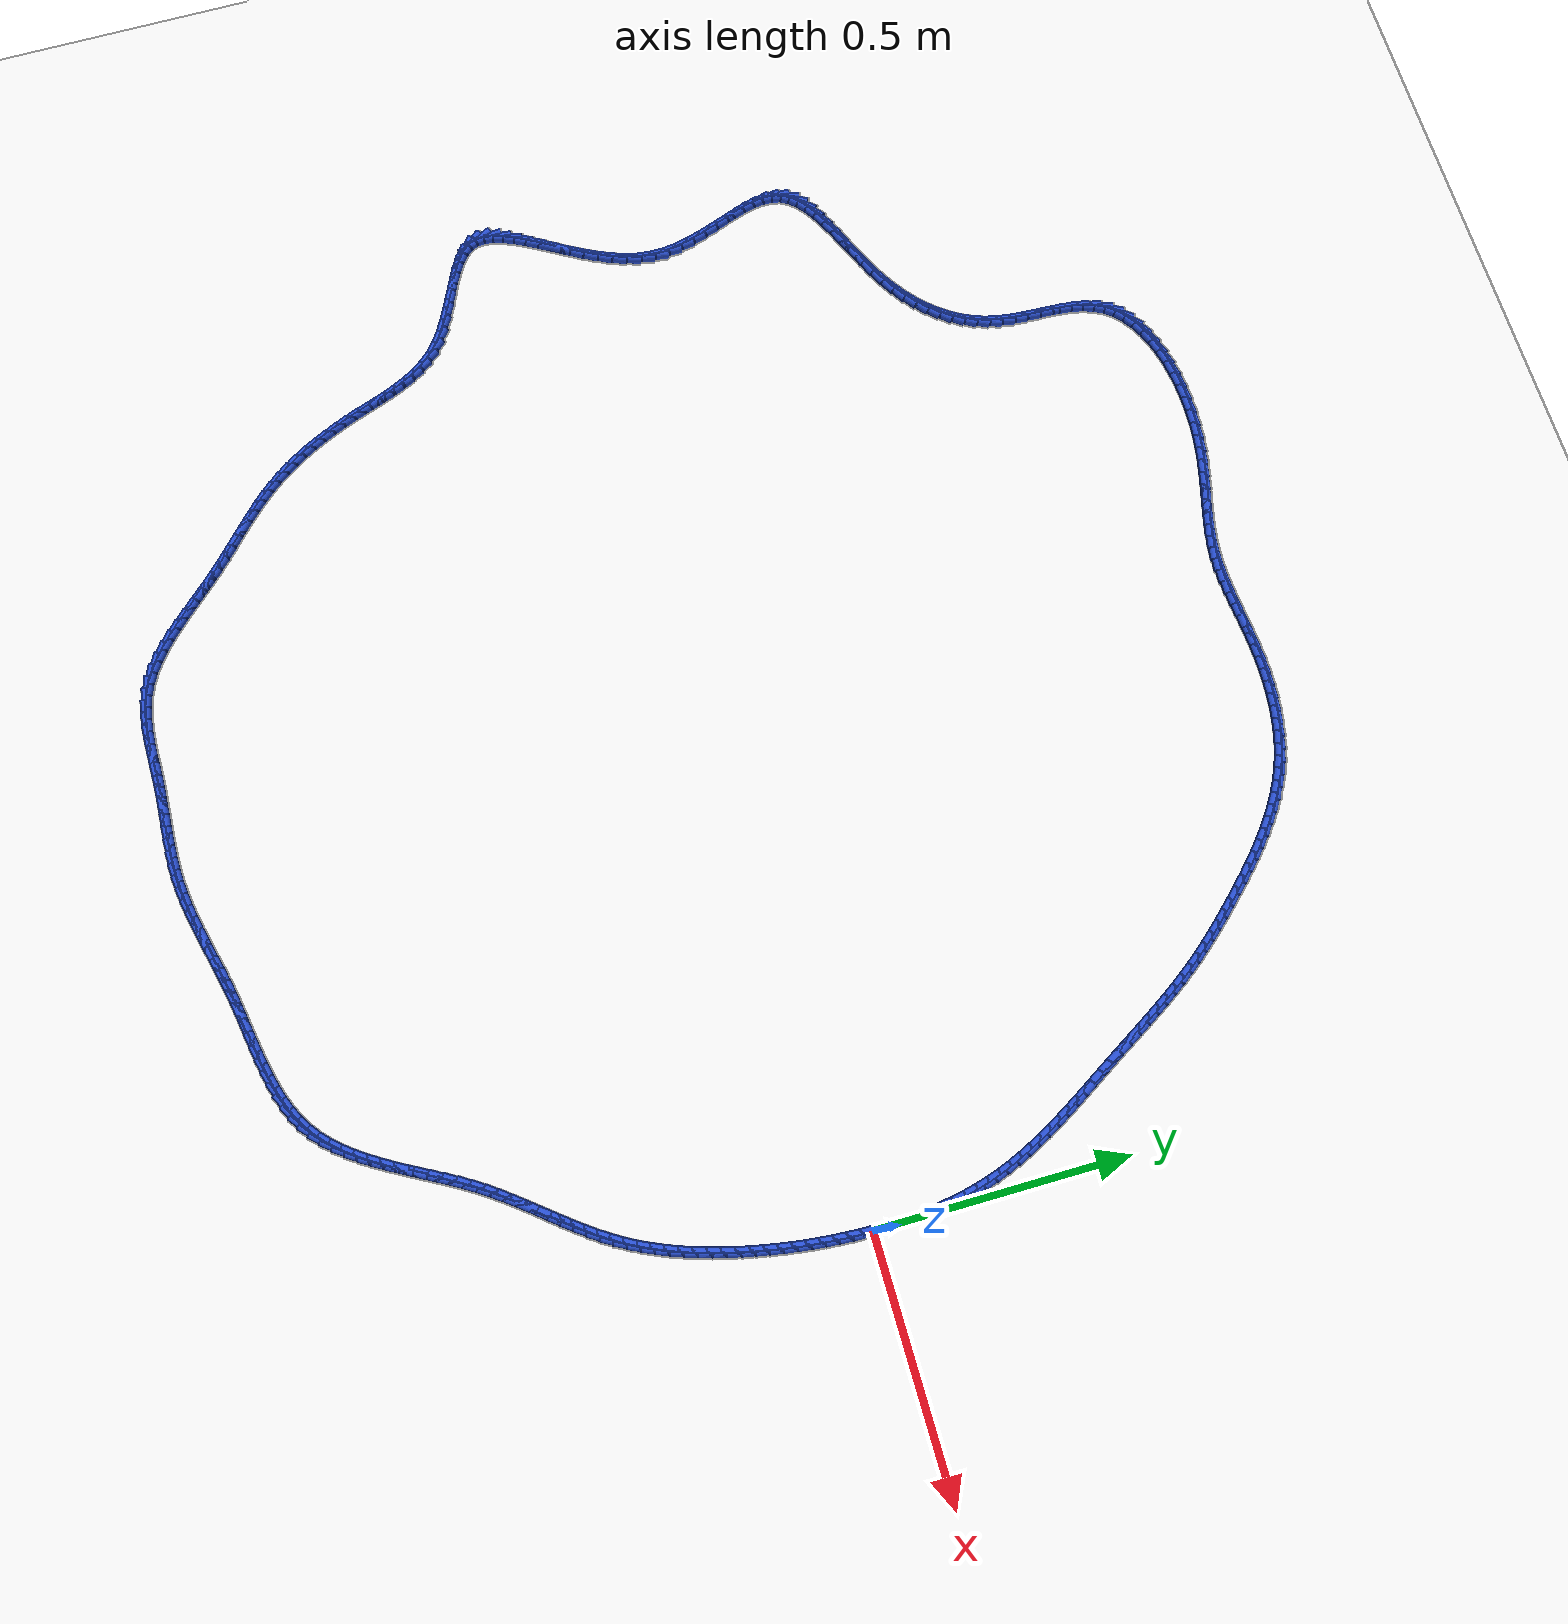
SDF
<sdf version="1.6">
 <world name="default">
  <light name="sun" type="directional">
   <pose>0 0 10 0 -0 0</pose>
   <diffuse>0.8 0.8 0.8 1</diffuse>
   <specular>0.2 0.2 0.2 1</specular>
   <attenuation>
    <range>1000</range>
    <constant>0.9</constant>
    <linear>0.01</linear>
    <quadratic>0.001</quadratic>
   </attenuation>
   <direction>-0.5 0.1 -0.9</direction>
  </light>
  <model name="ground_plane">
   <static>1</static>
   <link name="link">
    <collision name="collision">
     <geometry><plane><normal>0 0 1</normal><size>100 100</size></plane></geometry>
     <surface><friction><ode><mu>100</mu><mu2>50</mu2></ode></friction></surface>
    </collision>
    <visual name="visual">
     <cast_shadows>0</cast_shadows>
     <geometry><plane><normal>0 0 1</normal><size>100 100</size></plane></geometry>
     <material>
      <script><uri>file://media/materials/scripts/gazebo.material</uri><name>Gazebo/WhiteGlow</name></script>
     </material>
    </visual>
   </link>
  </model>
  <gravity>0 0 -9.8</gravity>
  <magnetic_field>6e-06 2.3e-05 -4.2e-05</magnetic_field>
  <atmosphere type="adiabatic"/>
  <physics name="default_physics" default="0" type="ode">
   <max_step_size>0.001</max_step_size>
   <real_time_factor>1</real_time_factor>
   <real_time_update_rate>1000</real_time_update_rate>
  </physics>
  <scene><ambient>0.4 0.4 0.4 1</ambient><background>0.7 0.7 0.7 1</background><shadows>1</shadows></scene>
  <spherical_coordinates>
   <surface_model>EARTH_WGS84</surface_model>
   <latitude_deg>0</latitude_deg>
   <longitude_deg>0</longitude_deg>
   <elevation>0</elevation>
   <heading_deg>0</heading_deg>
  </spherical_coordinates>
  <model name="line">
   <link name="link_0">
    <pose>-1.6479873021779667e-17 0.0 0.01 0 1.57 1.5654204564833294</pose>
    <collision name="collision">
     <geometry><cylinder><radius>0.01</radius><length>0.08</length></cylinder></geometry>
    </collision>
    <visual name="visual">
     <material>
      <script><name>Gazebo/Blue</name><uri>file://media/materials/scripts/gazebo.material</uri></script>
     </material>
     <geometry><cylinder><radius>0.01</radius><length>0.08</length></cylinder></geometry>
    </visual>
   </link>
   <link name="link_1">
    <pose>0.00013879050816110192 0.02581706088510633 0.01 0 1.57 -1.552005356154008</pose>
    <collision name="collision">
     <geometry><cylinder><radius>0.01</radius><length>0.08</length></cylinder></geometry>
    </collision>
    <visual name="visual">
     <material>
      <script><name>Gazebo/Blue</name><uri>file://media/materials/scripts/gazebo.material</uri></script>
     </material>
     <geometry><cylinder><radius>0.01</radius><length>0.08</length></cylinder></geometry>
    </visual>
   </link>
   <link name="link_2">
    <pose>-0.0003471206326306521 0.0516727740835173 0.01 0 1.57 -1.5254065276339013</pose>
    <collision name="collision">
     <geometry><cylinder><radius>0.01</radius><length>0.08</length></cylinder></geometry>
    </collision>
    <visual name="visual">
     <material>
      <script><name>Gazebo/Blue</name><uri>file://media/materials/scripts/gazebo.material</uri></script>
     </material>
     <geometry><cylinder><radius>0.01</radius><length>0.08</length></cylinder></geometry>
    </visual>
   </link>
   <link name="link_3">
    <pose>-0.001520814700794198 0.07751311598907709 0.01 0 1.57 -1.4962553160184355</pose>
    <collision name="collision">
     <geometry><cylinder><radius>0.01</radius><length>0.08</length></cylinder></geometry>
    </collision>
    <visual name="visual">
     <material>
      <script><name>Gazebo/Blue</name><uri>file://media/materials/scripts/gazebo.material</uri></script>
     </material>
     <geometry><cylinder><radius>0.01</radius><length>0.08</length></cylinder></geometry>
    </visual>
   </link>
   <link name="link_4">
    <pose>-0.003445372974748444 0.10328406299562987 0.01 0 1.57 -1.4644247783390028</pose>
    <collision name="collision">
     <geometry><cylinder><radius>0.01</radius><length>0.08</length></cylinder></geometry>
    </collision>
    <visual name="visual">
     <material>
      <script><name>Gazebo/Blue</name><uri>file://media/materials/scripts/gazebo.material</uri></script>
     </material>
     <geometry><cylinder><radius>0.01</radius><length>0.08</length></cylinder></geometry>
    </visual>
   </link>
   <link name="link_5">
    <pose>-0.006183876732912305 0.12893159149701983 0.01 0 1.57 -1.4297863929135664</pose>
    <collision name="collision">
     <geometry><cylinder><radius>0.01</radius><length>0.08</length></cylinder></geometry>
    </collision>
    <visual name="visual">
     <material>
      <script><name>Gazebo/Blue</name><uri>file://media/materials/scripts/gazebo.material</uri></script>
     </material>
     <geometry><cylinder><radius>0.01</radius><length>0.08</length></cylinder></geometry>
    </visual>
   </link>
   <link name="link_6">
    <pose>-0.009799407253704703 0.15440167788709117 0.01 0 1.57 -1.3922165311565011</pose>
    <collision name="collision">
     <geometry><cylinder><radius>0.01</radius><length>0.08</length></cylinder></geometry>
    </collision>
    <visual name="visual">
     <material>
      <script><name>Gazebo/Blue</name><uri>file://media/materials/scripts/gazebo.material</uri></script>
     </material>
     <geometry><cylinder><radius>0.01</radius><length>0.08</length></cylinder></geometry>
    </visual>
   </link>
   <link name="link_7">
    <pose>-0.01435504581554454 0.17964029855968802 0.01 0 1.57 -1.35160472331401</pose>
    <collision name="collision">
     <geometry><cylinder><radius>0.01</radius><length>0.08</length></cylinder></geometry>
    </collision>
    <visual name="visual">
     <material>
      <script><name>Gazebo/Blue</name><uri>file://media/materials/scripts/gazebo.material</uri></script>
     </material>
     <geometry><cylinder><radius>0.01</radius><length>0.08</length></cylinder></geometry>
    </visual>
   </link>
   <link name="link_8">
    <pose>-0.019913873696850735 0.20459342990865464 0.01 0 1.57 -1.3078639098746183</pose>
    <collision name="collision">
     <geometry><cylinder><radius>0.01</radius><length>0.08</length></cylinder></geometry>
    </collision>
    <visual name="visual">
     <material>
      <script><name>Gazebo/Blue</name><uri>file://media/materials/scripts/gazebo.material</uri></script>
     </material>
     <geometry><cylinder><radius>0.01</radius><length>0.08</length></cylinder></geometry>
    </visual>
   </link>
   <link name="link_9">
    <pose>-0.026538972176042196 0.22920704832783506 0.01 0 1.57 -1.261954005294418</pose>
    <collision name="collision">
     <geometry><cylinder><radius>0.01</radius><length>0.08</length></cylinder></geometry>
    </collision>
    <visual name="visual">
     <material>
      <script><name>Gazebo/Blue</name><uri>file://media/materials/scripts/gazebo.material</uri></script>
     </material>
     <geometry><cylinder><radius>0.01</radius><length>0.08</length></cylinder></geometry>
    </visual>
   </link>
   <link name="link_10">
    <pose>-0.03427036477463058 0.25343947586045384 0.01 0 1.57 -1.2187495711804412</pose>
    <collision name="collision">
     <geometry><cylinder><radius>0.01</radius><length>0.08</length></cylinder></geometry>
    </collision>
    <visual name="visual">
     <material>
      <script><name>Gazebo/Blue</name><uri>file://media/materials/scripts/gazebo.material</uri></script>
     </material>
     <geometry><cylinder><radius>0.01</radius><length>0.08</length></cylinder></geometry>
    </visual>
   </link>
   <link name="link_11">
    <pose>-0.04303837571493844 0.2773077700585919 0.01 0 1.57 -1.1798270908982167</pose>
    <collision name="collision">
     <geometry><cylinder><radius>0.01</radius><length>0.08</length></cylinder></geometry>
    </collision>
    <visual name="visual">
     <material>
      <script><name>Gazebo/Blue</name><uri>file://media/materials/scripts/gazebo.material</uri></script>
     </material>
     <geometry><cylinder><radius>0.01</radius><length>0.08</length></cylinder></geometry>
    </visual>
   </link>
   <link name="link_12">
    <pose>-0.05274074057202016 0.3008464371799679 0.01 0 1.57 -1.1452675998350514</pose>
    <collision name="collision">
     <geometry><cylinder><radius>0.01</radius><length>0.08</length></cylinder></geometry>
    </collision>
    <visual name="visual">
     <material>
      <script><name>Gazebo/Blue</name><uri>file://media/materials/scripts/gazebo.material</uri></script>
     </material>
     <geometry><cylinder><radius>0.01</radius><length>0.08</length></cylinder></geometry>
    </visual>
   </link>
   <link name="link_13">
    <pose>-0.0632751896257293 0.32408998631747243 0.01 0 1.57 -1.1150886530281037</pose>
    <collision name="collision">
     <geometry><cylinder><radius>0.01</radius><length>0.08</length></cylinder></geometry>
    </collision>
    <visual name="visual">
     <material>
      <script><name>Gazebo/Blue</name><uri>file://media/materials/scripts/gazebo.material</uri></script>
     </material>
     <geometry><cylinder><radius>0.01</radius><length>0.08</length></cylinder></geometry>
    </visual>
   </link>
   <link name="link_14">
    <pose>-0.07453945315591938 0.34707292656399574 0.01 0 1.57 -1.0892642495315623</pose>
    <collision name="collision">
     <geometry><cylinder><radius>0.01</radius><length>0.08</length></cylinder></geometry>
    </collision>
    <visual name="visual">
     <material>
      <script><name>Gazebo/Blue</name><uri>file://media/materials/scripts/gazebo.material</uri></script>
     </material>
     <geometry><cylinder><radius>0.01</radius><length>0.08</length></cylinder></geometry>
    </visual>
   </link>
   <link name="link_15">
    <pose>-0.0864312614424439 0.3698297670124281 0.01 0 1.57 -1.0677423304085614</pose>
    <collision name="collision">
     <geometry><cylinder><radius>0.01</radius><length>0.08</length></cylinder></geometry>
    </collision>
    <visual name="visual">
     <material>
      <script><name>Gazebo/Blue</name><uri>file://media/materials/scripts/gazebo.material</uri></script>
     </material>
     <geometry><cylinder><radius>0.01</radius><length>0.08</length></cylinder></geometry>
    </visual>
   </link>
   <link name="link_16">
    <pose>-0.09884834476515636 0.3923950167556597 0.01 0 1.57 -1.0504594010511847</pose>
    <collision name="collision">
     <geometry><cylinder><radius>0.01</radius><length>0.08</length></cylinder></geometry>
    </collision>
    <visual name="visual">
     <material>
      <script><name>Gazebo/Blue</name><uri>file://media/materials/scripts/gazebo.material</uri></script>
     </material>
     <geometry><cylinder><radius>0.01</radius><length>0.08</length></cylinder></geometry>
    </visual>
   </link>
   <link name="link_17">
    <pose>-0.11168843340391041 0.4148031848865813 0.01 0 1.57 -1.0373521458834554</pose>
    <collision name="collision">
     <geometry><cylinder><radius>0.01</radius><length>0.08</length></cylinder></geometry>
    </collision>
    <visual name="visual">
     <material>
      <script><name>Gazebo/Blue</name><uri>file://media/materials/scripts/gazebo.material</uri></script>
     </material>
     <geometry><cylinder><radius>0.01</radius><length>0.08</length></cylinder></geometry>
    </visual>
   </link>
   <link name="link_18">
    <pose>-0.12484925763855939 0.43708878049808275 0.01 0 1.57 -1.0283662225906132</pose>
    <collision name="collision">
     <geometry><cylinder><radius>0.01</radius><length>0.08</length></cylinder></geometry>
    </collision>
    <visual name="visual">
     <material>
      <script><name>Gazebo/Blue</name><uri>file://media/materials/scripts/gazebo.material</uri></script>
     </material>
     <geometry><cylinder><radius>0.01</radius><length>0.08</length></cylinder></geometry>
    </visual>
   </link>
   <link name="link_19">
    <pose>-0.13822854774895693 0.45928631268305464 0.01 0 1.57 -1.023462559176008</pose>
    <collision name="collision">
     <geometry><cylinder><radius>0.01</radius><length>0.08</length></cylinder></geometry>
    </collision>
    <visual name="visual">
     <material>
      <script><name>Gazebo/Blue</name><uri>file://media/materials/scripts/gazebo.material</uri></script>
     </material>
     <geometry><cylinder><radius>0.01</radius><length>0.08</length></cylinder></geometry>
    </visual>
   </link>
   <link name="link_20">
    <pose>-0.15172403401495654 0.48143029053438724 0.01 0 1.57 -1.0226214863067906</pose>
    <collision name="collision">
     <geometry><cylinder><radius>0.01</radius><length>0.08</length></cylinder></geometry>
    </collision>
    <visual name="visual">
     <material>
      <script><name>Gazebo/Blue</name><uri>file://media/materials/scripts/gazebo.material</uri></script>
     </material>
     <geometry><cylinder><radius>0.01</radius><length>0.08</length></cylinder></geometry>
    </visual>
   </link>
   <link name="link_21">
    <pose>-0.16523344671641177 0.5035552231449708 0.01 0 1.57 -1.0258405274097924</pose>
    <collision name="collision">
     <geometry><cylinder><radius>0.01</radius><length>0.08</length></cylinder></geometry>
    </collision>
    <visual name="visual">
     <material>
      <script><name>Gazebo/Blue</name><uri>file://media/materials/scripts/gazebo.material</uri></script>
     </material>
     <geometry><cylinder><radius>0.01</radius><length>0.08</length></cylinder></geometry>
    </visual>
   </link>
   <link name="link_22">
    <pose>-0.17865462096792287 0.5256955708049829 0.01 0 1.57 -1.0311594907561974</pose>
    <collision name="collision">
     <geometry><cylinder><radius>0.01</radius><length>0.08</length></cylinder></geometry>
    </collision>
    <visual name="visual">
     <material>
      <script><name>Gazebo/Blue</name><uri>file://media/materials/scripts/gazebo.material</uri></script>
     </material>
     <geometry><cylinder><radius>0.01</radius><length>0.08</length></cylinder></geometry>
    </visual>
   </link>
   <link name="link_23">
    <pose>-0.1919321180189764 0.5478640418357149 0.01 0 1.57 -1.0334885647334984</pose>
    <collision name="collision">
     <geometry><cylinder><radius>0.01</radius><length>0.08</length></cylinder></geometry>
    </collision>
    <visual name="visual">
     <material>
      <script><name>Gazebo/Blue</name><uri>file://media/materials/scripts/gazebo.material</uri></script>
     </material>
     <geometry><cylinder><radius>0.01</radius><length>0.08</length></cylinder></geometry>
    </visual>
   </link>
   <link name="link_24">
    <pose>-0.20513058125530645 0.5700174438746602 0.01 0 1.57 -1.0319988711001322</pose>
    <collision name="collision">
     <geometry><cylinder><radius>0.01</radius><length>0.08</length></cylinder></geometry>
    </collision>
    <visual name="visual">
     <material>
      <script><name>Gazebo/Blue</name><uri>file://media/materials/scripts/gazebo.material</uri></script>
     </material>
     <geometry><cylinder><radius>0.01</radius><length>0.08</length></cylinder></geometry>
    </visual>
   </link>
   <link name="link_25">
    <pose>-0.21833367757780164 0.5921037287249754 0.01 0 1.57 -1.0266655086733385</pose>
    <collision name="collision">
     <geometry><cylinder><radius>0.01</radius><length>0.08</length></cylinder></geometry>
    </collision>
    <visual name="visual">
     <material>
      <script><name>Gazebo/Blue</name><uri>file://media/materials/scripts/gazebo.material</uri></script>
     </material>
     <geometry><cylinder><radius>0.01</radius><length>0.08</length></cylinder></geometry>
    </visual>
   </link>
   <link name="link_26">
    <pose>-0.23162507388735043 0.6140708481898177 0.01 0 1.57 -1.01746261338969</pose>
    <collision name="collision">
     <geometry><cylinder><radius>0.01</radius><length>0.08</length></cylinder></geometry>
    </collision>
    <visual name="visual">
     <material>
      <script><name>Gazebo/Blue</name><uri>file://media/materials/scripts/gazebo.material</uri></script>
     </material>
     <geometry><cylinder><radius>0.01</radius><length>0.08</length></cylinder></geometry>
    </visual>
   </link>
   <link name="link_27">
    <pose>-0.2450884370848414 0.635866754072344 0.01 0 1.57 -1.0043657360217348</pose>
    <collision name="collision">
     <geometry><cylinder><radius>0.01</radius><length>0.08</length></cylinder></geometry>
    </collision>
    <visual name="visual">
     <material>
      <script><name>Gazebo/Blue</name><uri>file://media/materials/scripts/gazebo.material</uri></script>
     </material>
     <geometry><cylinder><radius>0.01</radius><length>0.08</length></cylinder></geometry>
    </visual>
   </link>
   <link name="link_28">
    <pose>-0.25880743407116313 0.657439398175711 0.01 0 1.57 -0.9873560394268667</pose>
    <collision name="collision">
     <geometry><cylinder><radius>0.01</radius><length>0.08</length></cylinder></geometry>
    </collision>
    <visual name="visual">
     <material>
      <script><name>Gazebo/Blue</name><uri>file://media/materials/scripts/gazebo.material</uri></script>
     </material>
     <geometry><cylinder><radius>0.01</radius><length>0.08</length></cylinder></geometry>
    </visual>
   </link>
   <link name="link_29">
    <pose>-0.27286573174720397 0.6787367323030751 0.01 0 1.57 -0.966426363254302</pose>
    <collision name="collision">
     <geometry><cylinder><radius>0.01</radius><length>0.08</length></cylinder></geometry>
    </collision>
    <visual name="visual">
     <material>
      <script><name>Gazebo/Blue</name><uri>file://media/materials/scripts/gazebo.material</uri></script>
     </material>
     <geometry><cylinder><radius>0.01</radius><length>0.08</length></cylinder></geometry>
    </visual>
   </link>
   <link name="link_30">
    <pose>-0.2873469970138525 0.699706708257594 0.01 0 1.57 -0.941654895026567</pose>
    <collision name="collision">
     <geometry><cylinder><radius>0.01</radius><length>0.08</length></cylinder></geometry>
    </collision>
    <visual name="visual">
     <material>
      <script><name>Gazebo/Blue</name><uri>file://media/materials/scripts/gazebo.material</uri></script>
     </material>
     <geometry><cylinder><radius>0.01</radius><length>0.08</length></cylinder></geometry>
    </visual>
   </link>
   <link name="link_31">
    <pose>-0.3023335885066445 0.7202983267427154 0.01 0 1.57 -0.9156896885942454</pose>
    <collision name="collision">
     <geometry><cylinder><radius>0.01</radius><length>0.08</length></cylinder></geometry>
    </collision>
    <visual name="visual">
     <material>
      <script><name>Gazebo/Blue</name><uri>file://media/materials/scripts/gazebo.material</uri></script>
     </material>
     <geometry><cylinder><radius>0.01</radius><length>0.08</length></cylinder></geometry>
    </visual>
   </link>
   <link name="link_32">
    <pose>-0.31785604619325664 0.7405021340212274 0.01 0 1.57 -0.8920092230248826</pose>
    <collision name="collision">
     <geometry><cylinder><radius>0.01</radius><length>0.08</length></cylinder></geometry>
    </collision>
    <visual name="visual">
     <material>
      <script><name>Gazebo/Blue</name><uri>file://media/materials/scripts/gazebo.material</uri></script>
     </material>
     <geometry><cylinder><radius>0.01</radius><length>0.08</length></cylinder></geometry>
    </visual>
   </link>
   <link name="link_33">
    <pose>-0.33387703514484834 0.7603630949787261 0.01 0 1.57 -0.8708939179314461</pose>
    <collision name="collision">
     <geometry><cylinder><radius>0.01</radius><length>0.08</length></cylinder></geometry>
    </collision>
    <visual name="visual">
     <material>
      <script><name>Gazebo/Blue</name><uri>file://media/materials/scripts/gazebo.material</uri></script>
     </material>
     <geometry><cylinder><radius>0.01</radius><length>0.08</length></cylinder></geometry>
    </visual>
   </link>
   <link name="link_34">
    <pose>-0.35035462740354545 0.7799298569567302 0.01 0 1.57 -0.8523707451338214</pose>
    <collision name="collision">
     <geometry><cylinder><radius>0.01</radius><length>0.08</length></cylinder></geometry>
    </collision>
    <visual name="visual">
     <material>
      <script><name>Gazebo/Blue</name><uri>file://media/materials/scripts/gazebo.material</uri></script>
     </material>
     <geometry><cylinder><radius>0.01</radius><length>0.08</length></cylinder></geometry>
    </visual>
   </link>
   <link name="link_35">
    <pose>-0.36724689501147334 0.7992510672967577 0.01 0 1.57 -0.8364481841553267</pose>
    <collision name="collision">
     <geometry><cylinder><radius>0.01</radius><length>0.08</length></cylinder></geometry>
    </collision>
    <visual name="visual">
     <material>
      <script><name>Gazebo/Blue</name><uri>file://media/materials/scripts/gazebo.material</uri></script>
     </material>
     <geometry><cylinder><radius>0.01</radius><length>0.08</length></cylinder></geometry>
    </visual>
   </link>
   <link name="link_36">
    <pose>-0.38451191001075796 0.8183753733403278 0.01 0 1.57 -0.8231200362365712</pose>
    <collision name="collision">
     <geometry><cylinder><radius>0.01</radius><length>0.08</length></cylinder></geometry>
    </collision>
    <visual name="visual">
     <material>
      <script><name>Gazebo/Blue</name><uri>file://media/materials/scripts/gazebo.material</uri></script>
     </material>
     <geometry><cylinder><radius>0.01</radius><length>0.08</length></cylinder></geometry>
    </visual>
   </link>
   <link name="link_37">
    <pose>-0.4021077444435248 0.8373514224289584 0.01 0 1.57 -0.8119673398129457</pose>
    <collision name="collision">
     <geometry><cylinder><radius>0.01</radius><length>0.08</length></cylinder></geometry>
    </collision>
    <visual name="visual">
     <material>
      <script><name>Gazebo/Blue</name><uri>file://media/materials/scripts/gazebo.material</uri></script>
     </material>
     <geometry><cylinder><radius>0.01</radius><length>0.08</length></cylinder></geometry>
    </visual>
   </link>
   <link name="link_38">
    <pose>-0.4199971539812612 0.8562176282533777 0.01 0 1.57 -0.798811067101024</pose>
    <collision name="collision">
     <geometry><cylinder><radius>0.01</radius><length>0.08</length></cylinder></geometry>
    </collision>
    <visual name="visual">
     <material>
      <script><name>Gazebo/Blue</name><uri>file://media/materials/scripts/gazebo.material</uri></script>
     </material>
     <geometry><cylinder><radius>0.01</radius><length>0.08</length></cylinder></geometry>
    </visual>
   </link>
   <link name="link_39">
    <pose>-0.4381913393459131 0.8749065528899727 0.01 0 1.57 -0.7811426018957505</pose>
    <collision name="collision">
     <geometry><cylinder><radius>0.01</radius><length>0.08</length></cylinder></geometry>
    </collision>
    <visual name="visual">
     <material>
      <script><name>Gazebo/Blue</name><uri>file://media/materials/scripts/gazebo.material</uri></script>
     </material>
     <geometry><cylinder><radius>0.01</radius><length>0.08</length></cylinder></geometry>
    </visual>
   </link>
   <link name="link_40">
    <pose>-0.456730123643245 0.8932882189915008 0.01 0 1.57 -0.7588236196741744</pose>
    <collision name="collision">
     <geometry><cylinder><radius>0.01</radius><length>0.08</length></cylinder></geometry>
    </collision>
    <visual name="visual">
     <material>
      <script><name>Gazebo/Blue</name><uri>file://media/materials/scripts/gazebo.material</uri></script>
     </material>
     <geometry><cylinder><radius>0.01</radius><length>0.08</length></cylinder></geometry>
    </visual>
   </link>
   <link name="link_41">
    <pose>-0.47565370156563785 0.9112318373002578 0.01 0 1.57 -0.7317024142300346</pose>
    <collision name="collision">
     <geometry><cylinder><radius>0.01</radius><length>0.08</length></cylinder></geometry>
    </collision>
    <visual name="visual">
     <material>
      <script><name>Gazebo/Blue</name><uri>file://media/materials/scripts/gazebo.material</uri></script>
     </material>
     <geometry><cylinder><radius>0.01</radius><length>0.08</length></cylinder></geometry>
    </visual>
   </link>
   <link name="link_42">
    <pose>-0.4950022678054731 0.9286066185585412 0.01 0 1.57 -0.6995943235205871</pose>
    <collision name="collision">
     <geometry><cylinder><radius>0.01</radius><length>0.08</length></cylinder></geometry>
    </collision>
    <visual name="visual">
     <material>
      <script><name>Gazebo/Blue</name><uri>file://media/materials/scripts/gazebo.material</uri></script>
     </material>
     <geometry><cylinder><radius>0.01</radius><length>0.08</length></cylinder></geometry>
    </visual>
   </link>
   <link name="link_43">
    <pose>-0.5148160170551314 0.9452817735086463 0.01 0 1.57 -0.6622983901922096</pose>
    <collision name="collision">
     <geometry><cylinder><radius>0.01</radius><length>0.08</length></cylinder></geometry>
    </collision>
    <visual name="visual">
     <material>
      <script><name>Gazebo/Blue</name><uri>file://media/materials/scripts/gazebo.material</uri></script>
     </material>
     <geometry><cylinder><radius>0.01</radius><length>0.08</length></cylinder></geometry>
    </visual>
   </link>
   <link name="link_44">
    <pose>-0.5351351440069936 0.9611265128928697 0.01 0 1.57 -0.6196201285562538</pose>
    <collision name="collision">
     <geometry><cylinder><radius>0.01</radius><length>0.08</length></cylinder></geometry>
    </collision>
    <visual name="visual">
     <material>
      <script><name>Gazebo/Blue</name><uri>file://media/materials/scripts/gazebo.material</uri></script>
     </material>
     <geometry><cylinder><radius>0.01</radius><length>0.08</length></cylinder></geometry>
    </visual>
   </link>
   <link name="link_45">
    <pose>-0.5559998433534409 0.9760100474535072 0.01 0 1.57 -0.5714019634579988</pose>
    <collision name="collision">
     <geometry><cylinder><radius>0.01</radius><length>0.08</length></cylinder></geometry>
    </collision>
    <visual name="visual">
     <material>
      <script><name>Gazebo/Blue</name><uri>file://media/materials/scripts/gazebo.material</uri></script>
     </material>
     <geometry><cylinder><radius>0.01</radius><length>0.08</length></cylinder></geometry>
    </visual>
   </link>
   <link name="link_46">
    <pose>-0.5774503097868543 0.9898015879328559 0.01 0 1.57 -0.5175621459052533</pose>
    <collision name="collision">
     <geometry><cylinder><radius>0.01</radius><length>0.08</length></cylinder></geometry>
    </collision>
    <visual name="visual">
     <material>
      <script><name>Gazebo/Blue</name><uri>file://media/materials/scripts/gazebo.material</uri></script>
     </material>
     <geometry><cylinder><radius>0.01</radius><length>0.08</length></cylinder></geometry>
    </visual>
   </link>
   <link name="link_47">
    <pose>-0.599526737999615 1.0023703450732118 0.01 0 1.57 -0.45814125110068626</pose>
    <collision name="collision">
     <geometry><cylinder><radius>0.01</radius><length>0.08</length></cylinder></geometry>
    </collision>
    <visual name="visual">
     <material>
      <script><name>Gazebo/Blue</name><uri>file://media/materials/scripts/gazebo.material</uri></script>
     </material>
     <geometry><cylinder><radius>0.01</radius><length>0.08</length></cylinder></geometry>
    </visual>
   </link>
   <link name="link_48">
    <pose>-0.6222693226841037 1.0135855296168714 0.01 0 1.57 -0.39475051642981374</pose>
    <collision name="collision">
     <geometry><cylinder><radius>0.01</radius><length>0.08</length></cylinder></geometry>
    </collision>
    <visual name="visual">
     <material>
      <script><name>Gazebo/Blue</name><uri>file://media/materials/scripts/gazebo.material</uri></script>
     </material>
     <geometry><cylinder><radius>0.01</radius><length>0.08</length></cylinder></geometry>
    </visual>
   </link>
   <link name="link_49">
    <pose>-0.6456992980306332 1.0233469028677804 0.01 0 1.57 -0.33352731708520483</pose>
    <collision name="collision">
     <geometry><cylinder><radius>0.01</radius><length>0.08</length></cylinder></geometry>
    </collision>
    <visual name="visual">
     <material>
      <script><name>Gazebo/Blue</name><uri>file://media/materials/scripts/gazebo.material</uri></script>
     </material>
     <geometry><cylinder><radius>0.01</radius><length>0.08</length></cylinder></geometry>
    </visual>
   </link>
   <link name="link_50">
    <pose>-0.6697582162471432 1.0316826156264276 0.01 0 1.57 -0.2760789925601923</pose>
    <collision name="collision">
     <geometry><cylinder><radius>0.01</radius><length>0.08</length></cylinder></geometry>
    </collision>
    <visual name="visual">
     <material>
      <script><name>Gazebo/Blue</name><uri>file://media/materials/scripts/gazebo.material</uri></script>
     </material>
     <geometry><cylinder><radius>0.01</radius><length>0.08</length></cylinder></geometry>
    </visual>
   </link>
   <link name="link_51">
    <pose>-0.6943667009412988 1.0386545404001797 0.01 0 1.57 -0.222350610748899</pose>
    <collision name="collision">
     <geometry><cylinder><radius>0.01</radius><length>0.08</length></cylinder></geometry>
    </collision>
    <visual name="visual">
     <material>
      <script><name>Gazebo/Blue</name><uri>file://media/materials/scripts/gazebo.material</uri></script>
     </material>
     <geometry><cylinder><radius>0.01</radius><length>0.08</length></cylinder></geometry>
    </visual>
   </link>
   <link name="link_52">
    <pose>-0.7194453756318744 1.0443245498396265 0.01 0 1.57 -0.1722095091716396</pose>
    <collision name="collision">
     <geometry><cylinder><radius>0.01</radius><length>0.08</length></cylinder></geometry>
    </collision>
    <visual name="visual">
     <material>
      <script><name>Gazebo/Blue</name><uri>file://media/materials/scripts/gazebo.material</uri></script>
     </material>
     <geometry><cylinder><radius>0.01</radius><length>0.08</length></cylinder></geometry>
    </visual>
   </link>
   <link name="link_53">
    <pose>-0.7449148638376442 1.0487545165953598 0.01 0 1.57 -0.12546931119351024</pose>
    <collision name="collision">
     <geometry><cylinder><radius>0.01</radius><length>0.08</length></cylinder></geometry>
    </collision>
    <visual name="visual">
     <material>
      <script><name>Gazebo/Blue</name><uri>file://media/materials/scripts/gazebo.material</uri></script>
     </material>
     <geometry><cylinder><radius>0.01</radius><length>0.08</length></cylinder></geometry>
    </visual>
   </link>
   <link name="link_54">
    <pose>-0.7706957890773829 1.052006313317971 0.01 0 1.57 -0.08190991088015818</pose>
    <collision name="collision">
     <geometry><cylinder><radius>0.01</radius><length>0.08</length></cylinder></geometry>
    </collision>
    <visual name="visual">
     <material>
      <script><name>Gazebo/Blue</name><uri>file://media/materials/scripts/gazebo.material</uri></script>
     </material>
     <geometry><cylinder><radius>0.01</radius><length>0.08</length></cylinder></geometry>
    </visual>
   </link>
   <link name="link_55">
    <pose>-0.7967087748698647 1.0541418126580515 0.01 0 1.57 -0.041293041287598295</pose>
    <collision name="collision">
     <geometry><cylinder><radius>0.01</radius><length>0.08</length></cylinder></geometry>
    </collision>
    <visual name="visual">
     <material>
      <script><name>Gazebo/Blue</name><uri>file://media/materials/scripts/gazebo.material</uri></script>
     </material>
     <geometry><cylinder><radius>0.01</radius><length>0.08</length></cylinder></geometry>
    </visual>
   </link>
   <link name="link_56">
    <pose>-0.8228744447338638 1.0552228872661922 0.01 0 1.57 -0.003373690575349256</pose>
    <collision name="collision">
     <geometry><cylinder><radius>0.01</radius><length>0.08</length></cylinder></geometry>
    </collision>
    <visual name="visual">
     <material>
      <script><name>Gazebo/Blue</name><uri>file://media/materials/scripts/gazebo.material</uri></script>
     </material>
     <geometry><cylinder><radius>0.01</radius><length>0.08</length></cylinder></geometry>
    </visual>
   </link>
   <link name="link_57">
    <pose>-0.8491134221881547 1.055311409792985 0.01 0 1.57 0.03177036529365382</pose>
    <collision name="collision">
     <geometry><cylinder><radius>0.01</radius><length>0.08</length></cylinder></geometry>
    </collision>
    <visual name="visual">
     <material>
      <script><name>Gazebo/Blue</name><uri>file://media/materials/scripts/gazebo.material</uri></script>
     </material>
     <geometry><cylinder><radius>0.01</radius><length>0.08</length></cylinder></geometry>
    </visual>
   </link>
   <link name="link_58">
    <pose>-0.8753478586387028 1.054477651625166 0.01 0 1.57 0.059612233916372506</pose>
    <collision name="collision">
     <geometry><cylinder><radius>0.01</radius><length>0.08</length></cylinder></geometry>
    </collision>
    <visual name="visual">
     <material>
      <script><name>Gazebo/Blue</name><uri>file://media/materials/scripts/gazebo.material</uri></script>
     </material>
     <geometry><cylinder><radius>0.01</radius><length>0.08</length></cylinder></geometry>
    </visual>
   </link>
   <link name="link_59">
    <pose>-0.901522389609654 1.0529154784679629 0.01 0 1.57 0.07664816412750622</pose>
    <collision name="collision">
     <geometry><cylinder><radius>0.01</radius><length>0.08</length></cylinder></geometry>
    </collision>
    <visual name="visual">
     <material>
      <script><name>Gazebo/Blue</name><uri>file://media/materials/scripts/gazebo.material</uri></script>
     </material>
     <geometry><cylinder><radius>0.01</radius><length>0.08</length></cylinder></geometry>
    </visual>
   </link>
   <link name="link_60">
    <pose>-0.9275987678306554 1.0509128486359425 0.01 0 1.57 0.08279923389420403</pose>
    <collision name="collision">
     <geometry><cylinder><radius>0.01</radius><length>0.08</length></cylinder></geometry>
    </collision>
    <visual name="visual">
     <material>
      <script><name>Gazebo/Blue</name><uri>file://media/materials/scripts/gazebo.material</uri></script>
     </material>
     <geometry><cylinder><radius>0.01</radius><length>0.08</length></cylinder></geometry>
    </visual>
   </link>
   <link name="link_61">
    <pose>-0.9535391754466055 1.0487600809225226 0.01 0 1.57 0.0779500344412997</pose>
    <collision name="collision">
     <geometry><cylinder><radius>0.01</radius><length>0.08</length></cylinder></geometry>
    </collision>
    <visual name="visual">
     <material>
      <script><name>Gazebo/Blue</name><uri>file://media/materials/scripts/gazebo.material</uri></script>
     </material>
     <geometry><cylinder><radius>0.01</radius><length>0.08</length></cylinder></geometry>
    </visual>
   </link>
   <link name="link_62">
    <pose>-0.979305794602404 1.0467474941211201 0.01 0 1.57 0.0618301584156629</pose>
    <collision name="collision">
     <geometry><cylinder><radius>0.01</radius><length>0.08</length></cylinder></geometry>
    </collision>
    <visual name="visual">
     <material>
      <script><name>Gazebo/Blue</name><uri>file://media/materials/scripts/gazebo.material</uri></script>
     </material>
     <geometry><cylinder><radius>0.01</radius><length>0.08</length></cylinder></geometry>
    </visual>
   </link>
   <link name="link_63">
    <pose>-1.00486080744295 1.0451654070251526 0.01 0 1.57 0.03402158652165355</pose>
    <collision name="collision">
     <geometry><cylinder><radius>0.01</radius><length>0.08</length></cylinder></geometry>
    </collision>
    <visual name="visual">
     <material>
      <script><name>Gazebo/Blue</name><uri>file://media/materials/scripts/gazebo.material</uri></script>
     </material>
     <geometry><cylinder><radius>0.01</radius><length>0.08</length></cylinder></geometry>
    </visual>
   </link>
   <link name="link_64">
    <pose>-1.0301663961131422 1.0443041384280367 0.01 0 1.57 -0.005990280040282577</pose>
    <collision name="collision">
     <geometry><cylinder><radius>0.01</radius><length>0.08</length></cylinder></geometry>
    </collision>
    <visual name="visual">
     <material>
      <script><name>Gazebo/Blue</name><uri>file://media/materials/scripts/gazebo.material</uri></script>
     </material>
     <geometry><cylinder><radius>0.01</radius><length>0.08</length></cylinder></geometry>
    </visual>
   </link>
   <link name="link_65">
    <pose>-1.0551847427578798 1.04445400712319 0.01 0 1.57 -0.0587065262863021</pose>
    <collision name="collision">
     <geometry><cylinder><radius>0.01</radius><length>0.08</length></cylinder></geometry>
    </collision>
    <visual name="visual">
     <material>
      <script><name>Gazebo/Blue</name><uri>file://media/materials/scripts/gazebo.material</uri></script>
     </material>
     <geometry><cylinder><radius>0.01</radius><length>0.08</length></cylinder></geometry>
    </visual>
   </link>
   <link name="link_66">
    <pose>-1.0798780295220622 1.04590533190403 0.01 0 1.57 -0.12041775519391185</pose>
    <collision name="collision">
     <geometry><cylinder><radius>0.01</radius><length>0.08</length></cylinder></geometry>
    </collision>
    <visual name="visual">
     <material>
      <script><name>Gazebo/Blue</name><uri>file://media/materials/scripts/gazebo.material</uri></script>
     </material>
     <geometry><cylinder><radius>0.01</radius><length>0.08</length></cylinder></geometry>
    </visual>
   </link>
   <link name="link_67">
    <pose>-1.1042383645350953 1.0488530100935698 0.01 0 1.57 -0.17428963430545558</pose>
    <collision name="collision">
     <geometry><cylinder><radius>0.01</radius><length>0.08</length></cylinder></geometry>
    </collision>
    <visual name="visual">
     <material>
      <script><name>Gazebo/Blue</name><uri>file://media/materials/scripts/gazebo.material</uri></script>
     </material>
     <geometry><cylinder><radius>0.01</radius><length>0.08</length></cylinder></geometry>
    </visual>
   </link>
   <link name="link_68">
    <pose>-1.1283796126108847 1.05310370778175 0.01 0 1.57 -0.21523904400579183</pose>
    <collision name="collision">
     <geometry><cylinder><radius>0.01</radius><length>0.08</length></cylinder></geometry>
    </collision>
    <visual name="visual">
     <material>
      <script><name>Gazebo/Blue</name><uri>file://media/materials/scripts/gazebo.material</uri></script>
     </material>
     <geometry><cylinder><radius>0.01</radius><length>0.08</length></cylinder></geometry>
    </visual>
   </link>
   <link name="link_69">
    <pose>-1.152446599690873 1.0583653689491557 0.01 0 1.57 -0.24287902745166387</pose>
    <collision name="collision">
     <geometry><cylinder><radius>0.01</radius><length>0.08</length></cylinder></geometry>
    </collision>
    <visual name="visual">
     <material>
      <script><name>Gazebo/Blue</name><uri>file://media/materials/scripts/gazebo.material</uri></script>
     </material>
     <geometry><cylinder><radius>0.01</radius><length>0.08</length></cylinder></geometry>
    </visual>
   </link>
   <link name="link_70">
    <pose>-1.1765841517220461 1.0643459375587025 0.01 0 1.57 -0.25727574184465374</pose>
    <collision name="collision">
     <geometry><cylinder><radius>0.01</radius><length>0.08</length></cylinder></geometry>
    </collision>
    <visual name="visual">
     <material>
      <script><name>Gazebo/Blue</name><uri>file://media/materials/scripts/gazebo.material</uri></script>
     </material>
     <geometry><cylinder><radius>0.01</radius><length>0.08</length></cylinder></geometry>
    </visual>
   </link>
   <link name="link_71">
    <pose>-1.2009370946513893 1.0707533575733053 0.01 0 1.57 -0.2587896713241554</pose>
    <collision name="collision">
     <geometry><cylinder><radius>0.01</radius><length>0.08</length></cylinder></geometry>
    </collision>
    <visual name="visual">
     <material>
      <script><name>Gazebo/Blue</name><uri>file://media/materials/scripts/gazebo.material</uri></script>
     </material>
     <geometry><cylinder><radius>0.01</radius><length>0.08</length></cylinder></geometry>
    </visual>
   </link>
   <link name="link_72">
    <pose>-1.2256502544258876 1.0772955729558782 0.01 0 1.57 -0.24797719030441243</pose>
    <collision name="collision">
     <geometry><cylinder><radius>0.01</radius><length>0.08</length></cylinder></geometry>
    </collision>
    <visual name="visual">
     <material>
      <script><name>Gazebo/Blue</name><uri>file://media/materials/scripts/gazebo.material</uri></script>
     </material>
     <geometry><cylinder><radius>0.01</radius><length>0.08</length></cylinder></geometry>
    </visual>
   </link>
   <link name="link_73">
    <pose>-1.2508684569925261 1.0836805276693373 0.01 0 1.57 -0.22555363552997876</pose>
    <collision name="collision">
     <geometry><cylinder><radius>0.01</radius><length>0.08</length></cylinder></geometry>
    </collision>
    <visual name="visual">
     <material>
      <script><name>Gazebo/Blue</name><uri>file://media/materials/scripts/gazebo.material</uri></script>
     </material>
     <geometry><cylinder><radius>0.01</radius><length>0.08</length></cylinder></geometry>
    </visual>
   </link>
   <link name="link_74">
    <pose>-1.276736528298291 1.0896161656765975 0.01 0 1.57 -0.19240354889719638</pose>
    <collision name="collision">
     <geometry><cylinder><radius>0.01</radius><length>0.08</length></cylinder></geometry>
    </collision>
    <visual name="visual">
     <material>
      <script><name>Gazebo/Blue</name><uri>file://media/materials/scripts/gazebo.material</uri></script>
     </material>
     <geometry><cylinder><radius>0.01</radius><length>0.08</length></cylinder></geometry>
    </visual>
   </link>
   <link name="link_75">
    <pose>-1.3033992942901667 1.0948104309405728 0.01 0 1.57 -0.14961987255452625</pose>
    <collision name="collision">
     <geometry><cylinder><radius>0.01</radius><length>0.08</length></cylinder></geometry>
    </collision>
    <visual name="visual">
     <material>
      <script><name>Gazebo/Blue</name><uri>file://media/materials/scripts/gazebo.material</uri></script>
     </material>
     <geometry><cylinder><radius>0.01</radius><length>0.08</length></cylinder></geometry>
    </visual>
   </link>
   <link name="link_76">
    <pose>-1.3310013963701117 1.098971349292782 0.01 0 1.57 -0.1007498563239477</pose>
    <collision name="collision">
     <geometry><cylinder><radius>0.01</radius><length>0.08</length></cylinder></geometry>
    </collision>
    <visual name="visual">
     <material>
      <script><name>Gazebo/Blue</name><uri>file://media/materials/scripts/gazebo.material</uri></script>
     </material>
     <geometry><cylinder><radius>0.01</radius><length>0.08</length></cylinder></geometry>
    </visual>
   </link>
   <link name="link_77">
    <pose>-1.3595693598524987 1.1018593456960684 0.01 0 1.57 -0.05186217491209351</pose>
    <collision name="collision">
     <geometry><cylinder><radius>0.01</radius><length>0.08</length></cylinder></geometry>
    </collision>
    <visual name="visual">
     <material>
      <script><name>Gazebo/Blue</name><uri>file://media/materials/scripts/gazebo.material</uri></script>
     </material>
     <geometry><cylinder><radius>0.01</radius><length>0.08</length></cylinder></geometry>
    </visual>
   </link>
   <link name="link_78">
    <pose>-1.3888089631166414 1.103377136151818 0.01 0 1.57 -0.0025106530164531646</pose>
    <collision name="collision">
     <geometry><cylinder><radius>0.01</radius><length>0.08</length></cylinder></geometry>
    </collision>
    <visual name="visual">
     <material>
      <script><name>Gazebo/Blue</name><uri>file://media/materials/scripts/gazebo.material</uri></script>
     </material>
     <geometry><cylinder><radius>0.01</radius><length>0.08</length></cylinder></geometry>
    </visual>
   </link>
   <link name="link_79">
    <pose>-1.4183720597675147 1.103451358985552 0.01 0 1.57 0.04880287275235447</pose>
    <collision name="collision">
     <geometry><cylinder><radius>0.01</radius><length>0.08</length></cylinder></geometry>
    </collision>
    <visual name="visual">
     <material>
      <script><name>Gazebo/Blue</name><uri>file://media/materials/scripts/gazebo.material</uri></script>
     </material>
     <geometry><cylinder><radius>0.01</radius><length>0.08</length></cylinder></geometry>
    </visual>
   </link>
   <link name="link_80">
    <pose>-1.4479105034100908 1.1020086525227895 0.01 0 1.57 0.10361967306458716</pose>
    <collision name="collision">
     <geometry><cylinder><radius>0.01</radius><length>0.08</length></cylinder></geometry>
    </collision>
    <visual name="visual">
     <material>
      <script><name>Gazebo/Blue</name><uri>file://media/materials/scripts/gazebo.material</uri></script>
     </material>
     <geometry><cylinder><radius>0.01</radius><length>0.08</length></cylinder></geometry>
    </visual>
   </link>
   <link name="link_81">
    <pose>-1.4770761476493453 1.0989756550890493 0.01 0 1.57 0.16363869534880243</pose>
    <collision name="collision">
     <geometry><cylinder><radius>0.01</radius><length>0.08</length></cylinder></geometry>
    </collision>
    <visual name="visual">
     <material>
      <script><name>Gazebo/Blue</name><uri>file://media/materials/scripts/gazebo.material</uri></script>
     </material>
     <geometry><cylinder><radius>0.01</radius><length>0.08</length></cylinder></geometry>
    </visual>
   </link>
   <link name="link_82">
    <pose>-1.5055208460902505 1.0942790050098519 0.01 0 1.57 0.2308257009730837</pose>
    <collision name="collision">
     <geometry><cylinder><radius>0.01</radius><length>0.08</length></cylinder></geometry>
    </collision>
    <visual name="visual">
     <material>
      <script><name>Gazebo/Blue</name><uri>file://media/materials/scripts/gazebo.material</uri></script>
     </material>
     <geometry><cylinder><radius>0.01</radius><length>0.08</length></cylinder></geometry>
    </visual>
   </link>
   <link name="link_83">
    <pose>-1.5328964523377795 1.0878453406107158 0.01 0 1.57 0.307512563078737</pose>
    <collision name="collision">
     <geometry><cylinder><radius>0.01</radius><length>0.08</length></cylinder></geometry>
    </collision>
    <visual name="visual">
     <material>
      <script><name>Gazebo/Blue</name><uri>file://media/materials/scripts/gazebo.material</uri></script>
     </material>
     <geometry><cylinder><radius>0.01</radius><length>0.08</length></cylinder></geometry>
    </visual>
   </link>
   <link name="link_84">
    <pose>-1.558854819996907 1.0796013002171616 0.01 0 1.57 0.39645827041986353</pose>
    <collision name="collision">
     <geometry><cylinder><radius>0.01</radius><length>0.08</length></cylinder></geometry>
    </collision>
    <visual name="visual">
     <material>
      <script><name>Gazebo/Blue</name><uri>file://media/materials/scripts/gazebo.material</uri></script>
     </material>
     <geometry><cylinder><radius>0.01</radius><length>0.08</length></cylinder></geometry>
    </visual>
   </link>
   <link name="link_85">
    <pose>-1.5830478026726058 1.0694735221547085 0.01 0 1.57 0.5007955728534997</pose>
    <collision name="collision">
     <geometry><cylinder><radius>0.01</radius><length>0.08</length></cylinder></geometry>
    </collision>
    <visual name="visual">
     <material>
      <script><name>Gazebo/Blue</name><uri>file://media/materials/scripts/gazebo.material</uri></script>
     </material>
     <geometry><cylinder><radius>0.01</radius><length>0.08</length></cylinder></geometry>
    </visual>
   </link>
   <link name="link_86">
    <pose>-1.6051272539698491 1.0573886447488754 0.01 0 1.57 0.6237054487606671</pose>
    <collision name="collision">
     <geometry><cylinder><radius>0.01</radius><length>0.08</length></cylinder></geometry>
    </collision>
    <visual name="visual">
     <material>
      <script><name>Gazebo/Blue</name><uri>file://media/materials/scripts/gazebo.material</uri></script>
     </material>
     <geometry><cylinder><radius>0.01</radius><length>0.08</length></cylinder></geometry>
    </visual>
   </link>
   <link name="link_87">
    <pose>-1.6247450274936113 1.0432733063251824 0.01 0 1.57 0.7675726295533489</pose>
    <collision name="collision">
     <geometry><cylinder><radius>0.01</radius><length>0.08</length></cylinder></geometry>
    </collision>
    <visual name="visual">
     <material>
      <script><name>Gazebo/Blue</name><uri>file://media/materials/scripts/gazebo.material</uri></script>
     </material>
     <geometry><cylinder><radius>0.01</radius><length>0.08</length></cylinder></geometry>
    </visual>
   </link>
   <link name="link_88">
    <pose>-1.6415529768488653 1.0270541452091486 0.01 0 1.57 0.9324387501027629</pose>
    <collision name="collision">
     <geometry><cylinder><radius>0.01</radius><length>0.08</length></cylinder></geometry>
    </collision>
    <visual name="visual">
     <material>
      <script><name>Gazebo/Blue</name><uri>file://media/materials/scripts/gazebo.material</uri></script>
     </material>
     <geometry><cylinder><radius>0.01</radius><length>0.08</length></cylinder></geometry>
    </visual>
   </link>
   <link name="link_89">
    <pose>-1.6552029556405852 1.0086577997262942 0.01 0 1.57 1.1119775000070906</pose>
    <collision name="collision">
     <geometry><cylinder><radius>0.01</radius><length>0.08</length></cylinder></geometry>
    </collision>
    <visual name="visual">
     <material>
      <script><name>Gazebo/Blue</name><uri>file://media/materials/scripts/gazebo.material</uri></script>
     </material>
     <geometry><cylinder><radius>0.01</radius><length>0.08</length></cylinder></geometry>
    </visual>
   </link>
   <link name="link_90">
    <pose>-1.6653922083407513 0.9880308849547086 0.01 0 1.57 1.2707455470443976</pose>
    <collision name="collision">
     <geometry><cylinder><radius>0.01</radius><length>0.08</length></cylinder></geometry>
    </collision>
    <visual name="visual">
     <material>
      <script><name>Gazebo/Blue</name><uri>file://media/materials/scripts/gazebo.material</uri></script>
     </material>
     <geometry><cylinder><radius>0.01</radius><length>0.08</length></cylinder></geometry>
    </visual>
   </link>
   <link name="link_91">
    <pose>-1.6724012274418916 0.9653767064074054 0.01 0 1.57 1.387139058297314</pose>
    <collision name="collision">
     <geometry><cylinder><radius>0.01</radius><length>0.08</length></cylinder></geometry>
    </collision>
    <visual name="visual">
     <material>
      <script><name>Gazebo/Blue</name><uri>file://media/materials/scripts/gazebo.material</uri></script>
     </material>
     <geometry><cylinder><radius>0.01</radius><length>0.08</length></cylinder></geometry>
    </visual>
   </link>
   <link name="link_92">
    <pose>-1.6769149858087204 0.9410765834765652 0.01 0 1.57 1.4651088340341443</pose>
    <collision name="collision">
     <geometry><cylinder><radius>0.01</radius><length>0.08</length></cylinder></geometry>
    </collision>
    <visual name="visual">
     <material>
      <script><name>Gazebo/Blue</name><uri>file://media/materials/scripts/gazebo.material</uri></script>
     </material>
     <geometry><cylinder><radius>0.01</radius><length>0.08</length></cylinder></geometry>
    </visual>
   </link>
   <link name="link_93">
    <pose>-1.6796265853830845 0.9155154132027641 0.01 0 1.57 1.5102537218789707</pose>
    <collision name="collision">
     <geometry><cylinder><radius>0.01</radius><length>0.08</length></cylinder></geometry>
    </collision>
    <visual name="visual">
     <material>
      <script><name>Gazebo/Blue</name><uri>file://media/materials/scripts/gazebo.material</uri></script>
     </material>
     <geometry><cylinder><radius>0.01</radius><length>0.08</length></cylinder></geometry>
    </visual>
   </link>
   <link name="link_94">
    <pose>-1.6812291281068312 0.8890780926265784 0.01 0 1.57 1.5267605478331683</pose>
    <collision name="collision">
     <geometry><cylinder><radius>0.01</radius><length>0.08</length></cylinder></geometry>
    </collision>
    <visual name="visual">
     <material>
      <script><name>Gazebo/Blue</name><uri>file://media/materials/scripts/gazebo.material</uri></script>
     </material>
     <geometry><cylinder><radius>0.01</radius><length>0.08</length></cylinder></geometry>
    </visual>
   </link>
   <link name="link_95">
    <pose>-1.6824157159218074 0.8621495187885849 0.01 0 1.57 1.5167067806565746</pose>
    <collision name="collision">
     <geometry><cylinder><radius>0.01</radius><length>0.08</length></cylinder></geometry>
    </collision>
    <visual name="visual">
     <material>
      <script><name>Gazebo/Blue</name><uri>file://media/materials/scripts/gazebo.material</uri></script>
     </material>
     <geometry><cylinder><radius>0.01</radius><length>0.08</length></cylinder></geometry>
    </visual>
   </link>
   <link name="link_96">
    <pose>-1.6838794507698611 0.8351145887293596 0.01 0 1.57 1.4800776946496819</pose>
    <collision name="collision">
     <geometry><cylinder><radius>0.01</radius><length>0.08</length></cylinder></geometry>
    </collision>
    <visual name="visual">
     <material>
      <script><name>Gazebo/Blue</name><uri>file://media/materials/scripts/gazebo.material</uri></script>
     </material>
     <geometry><cylinder><radius>0.01</radius><length>0.08</length></cylinder></geometry>
    </visual>
   </link>
   <link name="link_97">
    <pose>-1.6863134345928381 0.8083581994894784 0.01 0 1.57 1.4150398137562794</pose>
    <collision name="collision">
     <geometry><cylinder><radius>0.01</radius><length>0.08</length></cylinder></geometry>
    </collision>
    <visual name="visual">
     <material>
      <script><name>Gazebo/Blue</name><uri>file://media/materials/scripts/gazebo.material</uri></script>
     </material>
     <geometry><cylinder><radius>0.01</radius><length>0.08</length></cylinder></geometry>
    </visual>
   </link>
   <link name="link_98">
    <pose>-1.6904107693325863 0.782265248109518 0.01 0 1.57 1.3222461879575953</pose>
    <collision name="collision">
     <geometry><cylinder><radius>0.01</radius><length>0.08</length></cylinder></geometry>
    </collision>
    <visual name="visual">
     <material>
      <script><name>Gazebo/Blue</name><uri>file://media/materials/scripts/gazebo.material</uri></script>
     </material>
     <geometry><cylinder><radius>0.01</radius><length>0.08</length></cylinder></geometry>
    </visual>
   </link>
   <link name="link_99">
    <pose>-1.696777711091376 0.7571786073847002 0.01 0 1.57 1.2216126610356066</pose>
    <collision name="collision">
     <geometry><cylinder><radius>0.01</radius><length>0.08</length></cylinder></geometry>
    </collision>
    <visual name="visual">
     <material>
      <script><name>Gazebo/Blue</name><uri>file://media/materials/scripts/gazebo.material</uri></script>
     </material>
     <geometry><cylinder><radius>0.01</radius><length>0.08</length></cylinder></geometry>
    </visual>
   </link>
   <link name="link_100">
    <pose>-1.7055104701143942 0.7331943416005423 0.01 0 1.57 1.1222509827391267</pose>
    <collision name="collision">
     <geometry><cylinder><radius>0.01</radius><length>0.08</length></cylinder></geometry>
    </collision>
    <visual name="visual">
     <material>
      <script><name>Gazebo/Blue</name><uri>file://media/materials/scripts/gazebo.material</uri></script>
     </material>
     <geometry><cylinder><radius>0.01</radius><length>0.08</length></cylinder></geometry>
    </visual>
   </link>
   <link name="link_101">
    <pose>-1.7165196516778414 0.7103187017735131 0.01 0 1.57 1.0256795790060658</pose>
    <collision name="collision">
     <geometry><cylinder><radius>0.01</radius><length>0.08</length></cylinder></geometry>
    </collision>
    <visual name="visual">
     <material>
      <script><name>Gazebo/Blue</name><uri>file://media/materials/scripts/gazebo.material</uri></script>
     </material>
     <geometry><cylinder><radius>0.01</radius><length>0.08</length></cylinder></geometry>
    </visual>
   </link>
   <link name="link_102">
    <pose>-1.7297155947851501 0.6885578100720887 0.01 0 1.57 0.9331180591159318</pose>
    <collision name="collision">
     <geometry><cylinder><radius>0.01</radius><length>0.08</length></cylinder></geometry>
    </collision>
    <visual name="visual">
     <material>
      <script><name>Gazebo/Blue</name><uri>file://media/materials/scripts/gazebo.material</uri></script>
     </material>
     <geometry><cylinder><radius>0.01</radius><length>0.08</length></cylinder></geometry>
    </visual>
   </link>
   <link name="link_103">
    <pose>-1.745008638439756 0.667917788664745 0.01 0 1.57 0.8454274115639779</pose>
    <collision name="collision">
     <geometry><cylinder><radius>0.01</radius><length>0.08</length></cylinder></geometry>
    </collision>
    <visual name="visual">
     <material>
      <script><name>Gazebo/Blue</name><uri>file://media/materials/scripts/gazebo.material</uri></script>
     </material>
     <geometry><cylinder><radius>0.01</radius><length>0.08</length></cylinder></geometry>
    </visual>
   </link>
   <link name="link_104">
    <pose>-1.7623091216450915 0.6484047597199581 0.01 0 1.57 0.7631043013565872</pose>
    <collision name="collision">
     <geometry><cylinder><radius>0.01</radius><length>0.08</length></cylinder></geometry>
    </collision>
    <visual name="visual">
     <material>
      <script><name>Gazebo/Blue</name><uri>file://media/materials/scripts/gazebo.material</uri></script>
     </material>
     <geometry><cylinder><radius>0.01</radius><length>0.08</length></cylinder></geometry>
    </visual>
   </link>
   <link name="link_105">
    <pose>-1.78152738340459 0.6300248454062046 0.01 0 1.57 0.6863244239988429</pose>
    <collision name="collision">
     <geometry><cylinder><radius>0.01</radius><length>0.08</length></cylinder></geometry>
    </collision>
    <visual name="visual">
     <material>
      <script><name>Gazebo/Blue</name><uri>file://media/materials/scripts/gazebo.material</uri></script>
     </material>
     <geometry><cylinder><radius>0.01</radius><length>0.08</length></cylinder></geometry>
    </visual>
   </link>
   <link name="link_106">
    <pose>-1.8025737627216867 0.6127841678919608 0.01 0 1.57 0.6150115989685396</pose>
    <collision name="collision">
     <geometry><cylinder><radius>0.01</radius><length>0.08</length></cylinder></geometry>
    </collision>
    <visual name="visual">
     <material>
      <script><name>Gazebo/Blue</name><uri>file://media/materials/scripts/gazebo.material</uri></script>
     </material>
     <geometry><cylinder><radius>0.01</radius><length>0.08</length></cylinder></geometry>
    </visual>
   </link>
   <link name="link_107">
    <pose>-1.8253585985998129 0.5966888493457019 0.01 0 1.57 0.5489133650635474</pose>
    <collision name="collision">
     <geometry><cylinder><radius>0.01</radius><length>0.08</length></cylinder></geometry>
    </collision>
    <visual name="visual">
     <material>
      <script><name>Gazebo/Blue</name><uri>file://media/materials/scripts/gazebo.material</uri></script>
     </material>
     <geometry><cylinder><radius>0.01</radius><length>0.08</length></cylinder></geometry>
    </visual>
   </link>
   <link name="link_108">
    <pose>-1.849792193005085 0.5817449915681433 0.01 0 1.57 0.49101481316310697</pose>
    <collision name="collision">
     <geometry><cylinder><radius>0.01</radius><length>0.08</length></cylinder></geometry>
    </collision>
    <visual name="visual">
     <material>
      <script><name>Gazebo/Blue</name><uri>file://media/materials/scripts/gazebo.material</uri></script>
     </material>
     <geometry><cylinder><radius>0.01</radius><length>0.08</length></cylinder></geometry>
    </visual>
   </link>
   <link name="link_109">
    <pose>-1.87568178911386 0.5679020217163574 0.01 0 1.57 0.45046202257539814</pose>
    <collision name="collision">
     <geometry><cylinder><radius>0.01</radius><length>0.08</length></cylinder></geometry>
    </collision>
    <visual name="visual">
     <material>
      <script><name>Gazebo/Blue</name><uri>file://media/materials/scripts/gazebo.material</uri></script>
     </material>
     <geometry><cylinder><radius>0.01</radius><length>0.08</length></cylinder></geometry>
    </visual>
   </link>
   <link name="link_110">
    <pose>-1.9025065003591168 0.55492892007512 0.01 0 1.57 0.4271875500430103</pose>
    <collision name="collision">
     <geometry><cylinder><radius>0.01</radius><length>0.08</length></cylinder></geometry>
    </collision>
    <visual name="visual">
     <material>
      <script><name>Gazebo/Blue</name><uri>file://media/materials/scripts/gazebo.material</uri></script>
     </material>
     <geometry><cylinder><radius>0.01</radius><length>0.08</length></cylinder></geometry>
    </visual>
   </link>
   <link name="link_111">
    <pose>-1.9296802804238797 0.542558833929254 0.01 0 1.57 0.4201450552493722</pose>
    <collision name="collision">
     <geometry><cylinder><radius>0.01</radius><length>0.08</length></cylinder></geometry>
    </collision>
    <visual name="visual">
     <material>
      <script><name>Gazebo/Blue</name><uri>file://media/materials/scripts/gazebo.material</uri></script>
     </material>
     <geometry><cylinder><radius>0.01</radius><length>0.08</length></cylinder></geometry>
    </visual>
   </link>
   <link name="link_112">
    <pose>-1.9566170829911742 0.5305249105635832 0.01 0 1.57 0.42962929537691974</pose>
    <collision name="collision">
     <geometry><cylinder><radius>0.01</radius><length>0.08</length></cylinder></geometry>
    </collision>
    <visual name="visual">
     <material>
      <script><name>Gazebo/Blue</name><uri>file://media/materials/scripts/gazebo.material</uri></script>
     </material>
     <geometry><cylinder><radius>0.01</radius><length>0.08</length></cylinder></geometry>
    </visual>
   </link>
   <link name="link_113">
    <pose>-1.9827308617440225 0.5185602972629302 0.01 0 1.57 0.4574695651345775</pose>
    <collision name="collision">
     <geometry><cylinder><radius>0.01</radius><length>0.08</length></cylinder></geometry>
    </collision>
    <visual name="visual">
     <material>
      <script><name>Gazebo/Blue</name><uri>file://media/materials/scripts/gazebo.material</uri></script>
     </material>
     <geometry><cylinder><radius>0.01</radius><length>0.08</length></cylinder></geometry>
    </visual>
   </link>
   <link name="link_114">
    <pose>-2.007435570365451 0.5063981413121184 0.01 0 1.57 0.5074386706883938</pose>
    <collision name="collision">
     <geometry><cylinder><radius>0.01</radius><length>0.08</length></cylinder></geometry>
    </collision>
    <visual name="visual">
     <material>
      <script><name>Gazebo/Blue</name><uri>file://media/materials/scripts/gazebo.material</uri></script>
     </material>
     <geometry><cylinder><radius>0.01</radius><length>0.08</length></cylinder></geometry>
    </visual>
   </link>
   <link name="link_115">
    <pose>-2.030145162538483 0.49377158999597087 0.01 0 1.57 0.58589630635222</pose>
    <collision name="collision">
     <geometry><cylinder><radius>0.01</radius><length>0.08</length></cylinder></geometry>
    </collision>
    <visual name="visual">
     <material>
      <script><name>Gazebo/Blue</name><uri>file://media/materials/scripts/gazebo.material</uri></script>
     </material>
     <geometry><cylinder><radius>0.01</radius><length>0.08</length></cylinder></geometry>
    </visual>
   </link>
   <link name="link_116">
    <pose>-2.050273591946144 0.480413790599311 0.01 0 1.57 0.7023977280361631</pose>
    <collision name="collision">
     <geometry><cylinder><radius>0.01</radius><length>0.08</length></cylinder></geometry>
    </collision>
    <visual name="visual">
     <material>
      <script><name>Gazebo/Blue</name><uri>file://media/materials/scripts/gazebo.material</uri></script>
     </material>
     <geometry><cylinder><radius>0.01</radius><length>0.08</length></cylinder></geometry>
    </visual>
   </link>
   <link name="link_117">
    <pose>-2.0672348122714572 0.4660578904069619 0.01 0 1.57 0.8689006513348433</pose>
    <collision name="collision">
     <geometry><cylinder><radius>0.01</radius><length>0.08</length></cylinder></geometry>
    </collision>
    <visual name="visual">
     <material>
      <script><name>Gazebo/Blue</name><uri>file://media/materials/scripts/gazebo.material</uri></script>
     </material>
     <geometry><cylinder><radius>0.01</radius><length>0.08</length></cylinder></geometry>
    </visual>
   </link>
   <link name="link_118">
    <pose>-2.0804427771974465 0.45043703670374646 0.01 0 1.57 1.093607443347433</pose>
    <collision name="collision">
     <geometry><cylinder><radius>0.01</radius><length>0.08</length></cylinder></geometry>
    </collision>
    <visual name="visual">
     <material>
      <script><name>Gazebo/Blue</name><uri>file://media/materials/scripts/gazebo.material</uri></script>
     </material>
     <geometry><cylinder><radius>0.01</radius><length>0.08</length></cylinder></geometry>
    </visual>
   </link>
   <link name="link_119">
    <pose>-2.0893114404071387 0.43328437677448833 0.01 0 1.57 1.353847821729768</pose>
    <collision name="collision">
     <geometry><cylinder><radius>0.01</radius><length>0.08</length></cylinder></geometry>
    </collision>
    <visual name="visual">
     <material>
      <script><name>Gazebo/Blue</name><uri>file://media/materials/scripts/gazebo.material</uri></script>
     </material>
     <geometry><cylinder><radius>0.01</radius><length>0.08</length></cylinder></geometry>
    </visual>
   </link>
   <link name="link_120">
    <pose>-2.0934735546051293 0.4144015112249563 0.01 0 1.57 -1.5699843504026911</pose>
    <collision name="collision">
     <geometry><cylinder><radius>0.01</radius><length>0.08</length></cylinder></geometry>
    </collision>
    <visual name="visual">
     <material>
      <script><name>Gazebo/Blue</name><uri>file://media/materials/scripts/gazebo.material</uri></script>
     </material>
     <geometry><cylinder><radius>0.01</radius><length>0.08</length></cylinder></geometry>
    </visual>
   </link>
   <link name="link_121">
    <pose>-2.0934568835422844 0.39387005324031565 0.01 0 1.57 -1.4159245962872729</pose>
    <collision name="collision">
     <geometry><cylinder><radius>0.01</radius><length>0.08</length></cylinder></geometry>
    </collision>
    <visual name="visual">
     <material>
      <script><name>Gazebo/Blue</name><uri>file://media/materials/scripts/gazebo.material</uri></script>
     </material>
     <geometry><cylinder><radius>0.01</radius><length>0.08</length></cylinder></geometry>
    </visual>
   </link>
   <link name="link_122">
    <pose>-2.0900180091125615 0.37184320390258263 0.01 0 1.57 -1.3152844443918095</pose>
    <collision name="collision">
     <geometry><cylinder><radius>0.01</radius><length>0.08</length></cylinder></geometry>
    </collision>
    <visual name="visual">
     <material>
      <script><name>Gazebo/Blue</name><uri>file://media/materials/scripts/gazebo.material</uri></script>
     </material>
     <geometry><cylinder><radius>0.01</radius><length>0.08</length></cylinder></geometry>
    </visual>
   </link>
   <link name="link_123">
    <pose>-2.0839135133029143 0.3484741643228673 0.01 0 1.57 -1.2553798555123714</pose>
    <collision name="collision">
     <geometry><cylinder><radius>0.01</radius><length>0.08</length></cylinder></geometry>
    </collision>
    <visual name="visual">
     <material>
      <script><name>Gazebo/Blue</name><uri>file://media/materials/scripts/gazebo.material</uri></script>
     </material>
     <geometry><cylinder><radius>0.01</radius><length>0.08</length></cylinder></geometry>
    </visual>
   </link>
   <link name="link_124">
    <pose>-2.075899978100292 0.32391613561227883 0.01 0 1.57 -1.2268944485420152</pose>
    <collision name="collision">
     <geometry><cylinder><radius>0.01</radius><length>0.08</length></cylinder></geometry>
    </collision>
    <visual name="visual">
     <material>
      <script><name>Gazebo/Blue</name><uri>file://media/materials/scripts/gazebo.material</uri></script>
     </material>
     <geometry><cylinder><radius>0.01</radius><length>0.08</length></cylinder></geometry>
    </visual>
   </link>
   <link name="link_125">
    <pose>-2.066733985491649 0.2983223188819274 0.01 0 1.57 -1.224225904944185</pose>
    <collision name="collision">
     <geometry><cylinder><radius>0.01</radius><length>0.08</length></cylinder></geometry>
    </collision>
    <visual name="visual">
     <material>
      <script><name>Gazebo/Blue</name><uri>file://media/materials/scripts/gazebo.material</uri></script>
     </material>
     <geometry><cylinder><radius>0.01</radius><length>0.08</length></cylinder></geometry>
    </visual>
   </link>
   <link name="link_126">
    <pose>-2.057172117463934 0.27184591524292273 0.01 0 1.57 -1.2446667937695135</pose>
    <collision name="collision">
     <geometry><cylinder><radius>0.01</radius><length>0.08</length></cylinder></geometry>
    </collision>
    <visual name="visual">
     <material>
      <script><name>Gazebo/Blue</name><uri>file://media/materials/scripts/gazebo.material</uri></script>
     </material>
     <geometry><cylinder><radius>0.01</radius><length>0.08</length></cylinder></geometry>
    </visual>
   </link>
   <link name="link_127">
    <pose>-2.047970956004101 0.24464012580637465 0.01 0 1.57 -1.2876393451434307</pose>
    <collision name="collision">
     <geometry><cylinder><radius>0.01</radius><length>0.08</length></cylinder></geometry>
    </collision>
    <visual name="visual">
     <material>
      <script><name>Gazebo/Blue</name><uri>file://media/materials/scripts/gazebo.material</uri></script>
     </material>
     <geometry><cylinder><radius>0.01</radius><length>0.08</length></cylinder></geometry>
    </visual>
   </link>
   <link name="link_128">
    <pose>-2.0398870830991007 0.21685815168339279 0.01 0 1.57 -1.3540799251949462</pose>
    <collision name="collision">
     <geometry><cylinder><radius>0.01</radius><length>0.08</length></cylinder></geometry>
    </collision>
    <visual name="visual">
     <material>
      <script><name>Gazebo/Blue</name><uri>file://media/materials/scripts/gazebo.material</uri></script>
     </material>
     <geometry><cylinder><radius>0.01</radius><length>0.08</length></cylinder></geometry>
    </visual>
   </link>
   <link name="link_129">
    <pose>-2.0336770807358846 0.18865319398508715 0.01 0 1.57 -1.4457426536506794</pose>
    <collision name="collision">
     <geometry><cylinder><radius>0.01</radius><length>0.08</length></cylinder></geometry>
    </collision>
    <visual name="visual">
     <material>
      <script><name>Gazebo/Blue</name><uri>file://media/materials/scripts/gazebo.material</uri></script>
     </material>
     <geometry><cylinder><radius>0.01</radius><length>0.08</length></cylinder></geometry>
    </visual>
   </link>
   <link name="link_130">
    <pose>-2.0300975309014047 0.16017845382256743 0.01 0 1.57 -1.5640630805072957</pose>
    <collision name="collision">
     <geometry><cylinder><radius>0.01</radius><length>0.08</length></cylinder></geometry>
    </collision>
    <visual name="visual">
     <material>
      <script><name>Gazebo/Blue</name><uri>file://media/materials/scripts/gazebo.material</uri></script>
     </material>
     <geometry><cylinder><radius>0.01</radius><length>0.08</length></cylinder></geometry>
    </visual>
   </link>
   <link name="link_131">
    <pose>-2.029905015582613 0.1315871323069435 0.01 0 1.57 1.4409018151135338</pose>
    <collision name="collision">
     <geometry><cylinder><radius>0.01</radius><length>0.08</length></cylinder></geometry>
    </collision>
    <visual name="visual">
     <material>
      <script><name>Gazebo/Blue</name><uri>file://media/materials/scripts/gazebo.material</uri></script>
     </material>
     <geometry><cylinder><radius>0.01</radius><length>0.08</length></cylinder></geometry>
    </visual>
   </link>
   <link name="link_132">
    <pose>-2.0336359162464523 0.10302631273758886 0.01 0 1.57 1.3211197001781416</pose>
    <collision name="collision">
     <geometry><cylinder><radius>0.01</radius><length>0.08</length></cylinder></geometry>
    </collision>
    <visual name="visual">
     <material>
      <script><name>Gazebo/Blue</name><uri>file://media/materials/scripts/gazebo.material</uri></script>
     </material>
     <geometry><cylinder><radius>0.01</radius><length>0.08</length></cylinder></geometry>
    </visual>
   </link>
   <link name="link_133">
    <pose>-2.0408802742431877 0.07461678632940771 0.01 0 1.57 1.2264470802314729</pose>
    <collision name="collision">
     <geometry><cylinder><radius>0.01</radius><length>0.08</length></cylinder></geometry>
    </collision>
    <visual name="visual">
     <material>
      <script><name>Gazebo/Blue</name><uri>file://media/materials/scripts/gazebo.material</uri></script>
     </material>
     <geometry><cylinder><radius>0.01</radius><length>0.08</length></cylinder></geometry>
    </visual>
   </link>
   <link name="link_134">
    <pose>-2.0509739603708304 0.04647228269914175 0.01 0 1.57 1.1544216789153472</pose>
    <collision name="collision">
     <geometry><cylinder><radius>0.01</radius><length>0.08</length></cylinder></geometry>
    </collision>
    <visual name="visual">
     <material>
      <script><name>Gazebo/Blue</name><uri>file://media/materials/scripts/gazebo.material</uri></script>
     </material>
     <geometry><cylinder><radius>0.01</radius><length>0.08</length></cylinder></geometry>
    </visual>
   </link>
   <link name="link_135">
    <pose>-2.0632528421886875 0.018706531373550613 0.01 0 1.57 1.102369859617073</pose>
    <collision name="collision">
     <geometry><cylinder><radius>0.01</radius><length>0.08</length></cylinder></geometry>
    </collision>
    <visual name="visual">
     <material>
      <script><name>Gazebo/Blue</name><uri>file://media/materials/scripts/gazebo.material</uri></script>
     </material>
     <geometry><cylinder><radius>0.01</radius><length>0.08</length></cylinder></geometry>
    </visual>
   </link>
   <link name="link_136">
    <pose>-2.0770527872560662 -0.008566738120605013 0.01 0 1.57 1.068241240733676</pose>
    <collision name="collision">
     <geometry><cylinder><radius>0.01</radius><length>0.08</length></cylinder></geometry>
    </collision>
    <visual name="visual">
     <material>
      <script><name>Gazebo/Blue</name><uri>file://media/materials/scripts/gazebo.material</uri></script>
     </material>
     <geometry><cylinder><radius>0.01</radius><length>0.08</length></cylinder></geometry>
    </visual>
   </link>
   <link name="link_137">
    <pose>-2.0917096631322734 -0.035233796256563345 0.01 0 1.57 1.0509894995143927</pose>
    <collision name="collision">
     <geometry><cylinder><radius>0.01</radius><length>0.08</length></cylinder></geometry>
    </collision>
    <visual name="visual">
     <material>
      <script><name>Gazebo/Blue</name><uri>file://media/materials/scripts/gazebo.material</uri></script>
     </material>
     <geometry><cylinder><radius>0.01</radius><length>0.08</length></cylinder></geometry>
    </visual>
   </link>
   <link name="link_138">
    <pose>-2.1065593373766176 -0.06118091350756542 0.01 0 1.57 1.0508161467348716</pose>
    <collision name="collision">
     <geometry><cylinder><radius>0.01</radius><length>0.08</length></cylinder></geometry>
    </collision>
    <visual name="visual">
     <material>
      <script><name>Gazebo/Blue</name><uri>file://media/materials/scripts/gazebo.material</uri></script>
     </material>
     <geometry><cylinder><radius>0.01</radius><length>0.08</length></cylinder></geometry>
    </visual>
   </link>
   <link name="link_139">
    <pose>-2.1209376775484037 -0.08629436034684909 0.01 0 1.57 1.0694937413865677</pose>
    <collision name="collision">
     <geometry><cylinder><radius>0.01</radius><length>0.08</length></cylinder></geometry>
    </collision>
    <visual name="visual">
     <material>
      <script><name>Gazebo/Blue</name><uri>file://media/materials/scripts/gazebo.material</uri></script>
     </material>
     <geometry><cylinder><radius>0.01</radius><length>0.08</length></cylinder></geometry>
    </visual>
   </link>
   <link name="link_140">
    <pose>-2.1341805512069403 -0.11046040724765455 0.01 0 1.57 1.11093631890971</pose>
    <collision name="collision">
     <geometry><cylinder><radius>0.01</radius><length>0.08</length></cylinder></geometry>
    </collision>
    <visual name="visual">
     <material>
      <script><name>Gazebo/Blue</name><uri>file://media/materials/scripts/gazebo.material</uri></script>
     </material>
     <geometry><cylinder><radius>0.01</radius><length>0.08</length></cylinder></geometry>
    </visual>
   </link>
   <link name="link_141">
    <pose>-2.1456238259115343 -0.13356532468322185 0.01 0 1.57 1.1821590677180247</pose>
    <collision name="collision">
     <geometry><cylinder><radius>0.01</radius><length>0.08</length></cylinder></geometry>
    </collision>
    <visual name="visual">
     <material>
      <script><name>Gazebo/Blue</name><uri>file://media/materials/scripts/gazebo.material</uri></script>
     </material>
     <geometry><cylinder><radius>0.01</radius><length>0.08</length></cylinder></geometry>
    </visual>
   </link>
   <link name="link_142">
    <pose>-2.1546033692214936 -0.15549538312678918 0.01 0 1.57 1.294552981076173</pose>
    <collision name="collision">
     <geometry><cylinder><radius>0.01</radius><length>0.08</length></cylinder></geometry>
    </collision>
    <visual name="visual">
     <material>
      <script><name>Gazebo/Blue</name><uri>file://media/materials/scripts/gazebo.material</uri></script>
     </material>
     <geometry><cylinder><radius>0.01</radius><length>0.08</length></cylinder></geometry>
    </visual>
   </link>
   <link name="link_143">
    <pose>-2.1604550486961243 -0.17613685305159713 0.01 0 1.57 1.4641456755745184</pose>
    <collision name="collision">
     <geometry><cylinder><radius>0.01</radius><length>0.08</length></cylinder></geometry>
    </collision>
    <visual name="visual">
     <material>
      <script><name>Gazebo/Blue</name><uri>file://media/materials/scripts/gazebo.material</uri></script>
     </material>
     <geometry><cylinder><radius>0.01</radius><length>0.08</length></cylinder></geometry>
    </visual>
   </link>
   <link name="link_144">
    <pose>-2.1625147318947335 -0.1953760049308839 0.01 0 1.57 -1.4363955682429752</pose>
    <collision name="collision">
     <geometry><cylinder><radius>0.01</radius><length>0.08</length></cylinder></geometry>
    </collision>
    <visual name="visual">
     <material>
      <script><name>Gazebo/Blue</name><uri>file://media/materials/scripts/gazebo.material</uri></script>
     </material>
     <geometry><cylinder><radius>0.01</radius><length>0.08</length></cylinder></geometry>
    </visual>
   </link>
   <link name="link_145">
    <pose>-2.160118286376629 -0.2130991092378901 0.01 0 1.57 -1.1340677833362196</pose>
    <collision name="collision">
     <geometry><cylinder><radius>0.01</radius><length>0.08</length></cylinder></geometry>
    </collision>
    <visual name="visual">
     <material>
      <script><name>Gazebo/Blue</name><uri>file://media/materials/scripts/gazebo.material</uri></script>
     </material>
     <geometry><cylinder><radius>0.01</radius><length>0.08</length></cylinder></geometry>
    </visual>
   </link>
   <link name="link_146">
    <pose>-2.1526054995437276 -0.22919367993556916 0.01 0 1.57 -0.8480576584103328</pose>
    <collision name="collision">
     <geometry><cylinder><radius>0.01</radius><length>0.08</length></cylinder></geometry>
    </collision>
    <visual name="visual">
     <material>
      <script><name>Gazebo/Blue</name><uri>file://media/materials/scripts/gazebo.material</uri></script>
     </material>
     <geometry><cylinder><radius>0.01</radius><length>0.08</length></cylinder></geometry>
    </visual>
   </link>
   <link name="link_147">
    <pose>-2.139808891464023 -0.2437035403246617 0.01 0 1.57 -0.6550688421341406</pose>
    <collision name="collision">
     <geometry><cylinder><radius>0.01</radius><length>0.08</length></cylinder></geometry>
    </collision>
    <visual name="visual">
     <material>
      <script><name>Gazebo/Blue</name><uri>file://media/materials/scripts/gazebo.material</uri></script>
     </material>
     <geometry><cylinder><radius>0.01</radius><length>0.08</length></cylinder></geometry>
    </visual>
   </link>
   <link name="link_148">
    <pose>-2.122528019616311 -0.2569792865011802 0.01 0 1.57 -0.5374556325292339</pose>
    <collision name="collision">
     <geometry><cylinder><radius>0.01</radius><length>0.08</length></cylinder></geometry>
    </collision>
    <visual name="visual">
     <material>
      <script><name>Gazebo/Blue</name><uri>file://media/materials/scripts/gazebo.material</uri></script>
     </material>
     <geometry><cylinder><radius>0.01</radius><length>0.08</length></cylinder></geometry>
    </visual>
   </link>
   <link name="link_149">
    <pose>-2.101674967354991 -0.2694072110885071 0.01 0 1.57 -0.470760944810114</pose>
    <collision name="collision">
     <geometry><cylinder><radius>0.01</radius><length>0.08</length></cylinder></geometry>
    </collision>
    <visual name="visual">
     <material>
      <script><name>Gazebo/Blue</name><uri>file://media/materials/scripts/gazebo.material</uri></script>
     </material>
     <geometry><cylinder><radius>0.01</radius><length>0.08</length></cylinder></geometry>
    </visual>
   </link>
   <link name="link_150">
    <pose>-2.0781618180344648 -0.2813736067100233 0.01 0 1.57 -0.43995773170237773</pose>
    <collision name="collision">
     <geometry><cylinder><radius>0.01</radius><length>0.08</length></cylinder></geometry>
    </collision>
    <visual name="visual">
     <material>
      <script><name>Gazebo/Blue</name><uri>file://media/materials/scripts/gazebo.material</uri></script>
     </material>
     <geometry><cylinder><radius>0.01</radius><length>0.08</length></cylinder></geometry>
    </visual>
   </link>
   <link name="link_151">
    <pose>-2.0529006550091338 -0.29326476598911094 0.01 0 1.57 -0.4373686161639445</pose>
    <collision name="collision">
     <geometry><cylinder><radius>0.01</radius><length>0.08</length></cylinder></geometry>
    </collision>
    <visual name="visual">
     <material>
      <script><name>Gazebo/Blue</name><uri>file://media/materials/scripts/gazebo.material</uri></script>
     </material>
     <geometry><cylinder><radius>0.01</radius><length>0.08</length></cylinder></geometry>
    </visual>
   </link>
   <link name="link_152">
    <pose>-2.0268035616333977 -0.30546698154915203 0.01 0 1.57 -0.4602320616607585</pose>
    <collision name="collision">
     <geometry><cylinder><radius>0.01</radius><length>0.08</length></cylinder></geometry>
    </collision>
    <visual name="visual">
     <material>
      <script><name>Gazebo/Blue</name><uri>file://media/materials/scripts/gazebo.material</uri></script>
     </material>
     <geometry><cylinder><radius>0.01</radius><length>0.08</length></cylinder></geometry>
    </visual>
   </link>
   <link name="link_153">
    <pose>-2.0007826212616595 -0.3183665460135275 0.01 0 1.57 -0.5094200103748132</pose>
    <collision name="collision">
     <geometry><cylinder><radius>0.01</radius><length>0.08</length></cylinder></geometry>
    </collision>
    <visual name="visual">
     <material>
      <script><name>Gazebo/Blue</name><uri>file://media/materials/scripts/gazebo.material</uri></script>
     </material>
     <geometry><cylinder><radius>0.01</radius><length>0.08</length></cylinder></geometry>
    </visual>
   </link>
   <link name="link_154">
    <pose>-1.9757499172483184 -0.3323497520056195 0.01 0 1.57 -0.5889462581901332</pose>
    <collision name="collision">
     <geometry><cylinder><radius>0.01</radius><length>0.08</length></cylinder></geometry>
    </collision>
    <visual name="visual">
     <material>
      <script><name>Gazebo/Blue</name><uri>file://media/materials/scripts/gazebo.material</uri></script>
     </material>
     <geometry><cylinder><radius>0.01</radius><length>0.08</length></cylinder></geometry>
    </visual>
   </link>
   <link name="link_155">
    <pose>-1.952617532947778 -0.3478028921488093 0.01 0 1.57 -0.703994968441637</pose>
    <collision name="collision">
     <geometry><cylinder><radius>0.01</radius><length>0.08</length></cylinder></geometry>
    </collision>
    <visual name="visual">
     <material>
      <script><name>Gazebo/Blue</name><uri>file://media/materials/scripts/gazebo.material</uri></script>
     </material>
     <geometry><cylinder><radius>0.01</radius><length>0.08</length></cylinder></geometry>
    </visual>
   </link>
   <link name="link_156">
    <pose>-1.9322564430636773 -0.36509232169495687 0.01 0 1.57 -0.8326262918655828</pose>
    <collision name="collision">
     <geometry><cylinder><radius>0.01</radius><length>0.08</length></cylinder></geometry>
    </collision>
    <visual name="visual">
     <material>
      <script><name>Gazebo/Blue</name><uri>file://media/materials/scripts/gazebo.material</uri></script>
     </material>
     <geometry><cylinder><radius>0.01</radius><length>0.08</length></cylinder></geometry>
    </visual>
   </link>
   <link name="link_157">
    <pose>-1.9148341274855512 -0.3842432064573561 0.01 0 1.57 -0.9478546371311215</pose>
    <collision name="collision">
     <geometry><cylinder><radius>0.01</radius><length>0.08</length></cylinder></geometry>
    </collision>
    <visual name="visual">
     <material>
      <script><name>Gazebo/Blue</name><uri>file://media/materials/scripts/gazebo.material</uri></script>
     </material>
     <geometry><cylinder><radius>0.01</radius><length>0.08</length></cylinder></geometry>
    </visual>
   </link>
   <link name="link_158">
    <pose>-1.8999274193360196 -0.40499425322394583 0.01 0 1.57 -1.0443456720319624</pose>
    <collision name="collision">
     <geometry><cylinder><radius>0.01</radius><length>0.08</length></cylinder></geometry>
    </collision>
    <visual name="visual">
     <material>
      <script><name>Gazebo/Blue</name><uri>file://media/materials/scripts/gazebo.material</uri></script>
     </material>
     <geometry><cylinder><radius>0.01</radius><length>0.08</length></cylinder></geometry>
    </visual>
   </link>
   <link name="link_159">
    <pose>-1.8870948292004366 -0.42707528249654036 0.01 0 1.57 -1.120037500365324</pose>
    <collision name="collision">
     <geometry><cylinder><radius>0.01</radius><length>0.08</length></cylinder></geometry>
    </collision>
    <visual name="visual">
     <material>
      <script><name>Gazebo/Blue</name><uri>file://media/materials/scripts/gazebo.material</uri></script>
     </material>
     <geometry><cylinder><radius>0.01</radius><length>0.08</length></cylinder></geometry>
    </visual>
   </link>
   <link name="link_160">
    <pose>-1.875894867664154 -0.4502161147769559 0.01 0 1.57 -1.1746600822204103</pose>
    <collision name="collision">
     <geometry><cylinder><radius>0.01</radius><length>0.08</length></cylinder></geometry>
    </collision>
    <visual name="visual">
     <material>
      <script><name>Gazebo/Blue</name><uri>file://media/materials/scripts/gazebo.material</uri></script>
     </material>
     <geometry><cylinder><radius>0.01</radius><length>0.08</length></cylinder></geometry>
    </visual>
   </link>
   <link name="link_161">
    <pose>-1.8658860453125246 -0.4741465705670089 0.01 0 1.57 -1.2087859333828395</pose>
    <collision name="collision">
     <geometry><cylinder><radius>0.01</radius><length>0.08</length></cylinder></geometry>
    </collision>
    <visual name="visual">
     <material>
      <script><name>Gazebo/Blue</name><uri>file://media/materials/scripts/gazebo.material</uri></script>
     </material>
     <geometry><cylinder><radius>0.01</radius><length>0.08</length></cylinder></geometry>
    </visual>
   </link>
   <link name="link_162">
    <pose>-1.8566268727309008 -0.49859647036851334 0.01 0 1.57 -1.2231164719898269</pose>
    <collision name="collision">
     <geometry><cylinder><radius>0.01</radius><length>0.08</length></cylinder></geometry>
    </collision>
    <visual name="visual">
     <material>
      <script><name>Gazebo/Blue</name><uri>file://media/materials/scripts/gazebo.material</uri></script>
     </material>
     <geometry><cylinder><radius>0.01</radius><length>0.08</length></cylinder></geometry>
    </visual>
   </link>
   <link name="link_163">
    <pose>-1.8476758605046362 -0.5232956346832867 0.01 0 1.57 -1.2180787410710474</pose>
    <collision name="collision">
     <geometry><cylinder><radius>0.01</radius><length>0.08</length></cylinder></geometry>
    </collision>
    <visual name="visual">
     <material>
      <script><name>Gazebo/Blue</name><uri>file://media/materials/scripts/gazebo.material</uri></script>
     </material>
     <geometry><cylinder><radius>0.01</radius><length>0.08</length></cylinder></geometry>
    </visual>
   </link>
   <link name="link_164">
    <pose>-1.838591519219083 -0.5479738840131427 0.01 0 1.57 -1.1957740040604863</pose>
    <collision name="collision">
     <geometry><cylinder><radius>0.01</radius><length>0.08</length></cylinder></geometry>
    </collision>
    <visual name="visual">
     <material>
      <script><name>Gazebo/Blue</name><uri>file://media/materials/scripts/gazebo.material</uri></script>
     </material>
     <geometry><cylinder><radius>0.01</radius><length>0.08</length></cylinder></geometry>
    </visual>
   </link>
   <link name="link_165">
    <pose>-1.828981615486321 -0.5723860424745641 0.01 0 1.57 -1.16726221935054</pose>
    <collision name="collision">
     <geometry><cylinder><radius>0.01</radius><length>0.08</length></cylinder></geometry>
    </collision>
    <visual name="visual">
     <material>
      <script><name>Gazebo/Blue</name><uri>file://media/materials/scripts/gazebo.material</uri></script>
     </material>
     <geometry><cylinder><radius>0.01</radius><length>0.08</length></cylinder></geometry>
    </visual>
   </link>
   <link name="link_166">
    <pose>-1.818719254647977 -0.596421626886433 0.01 0 1.57 -1.1361766460265685</pose>
    <collision name="collision">
     <geometry><cylinder><radius>0.01</radius><length>0.08</length></cylinder></geometry>
    </collision>
    <visual name="visual">
     <material>
      <script><name>Gazebo/Blue</name><uri>file://media/materials/scripts/gazebo.material</uri></script>
     </material>
     <geometry><cylinder><radius>0.01</radius><length>0.08</length></cylinder></geometry>
    </visual>
   </link>
   <link name="link_167">
    <pose>-1.8077664945409855 -0.6200153086215839 0.01 0 1.57 -1.1023852012523034</pose>
    <collision name="collision">
     <geometry><cylinder><radius>0.01</radius><length>0.08</length></cylinder></geometry>
    </collision>
    <visual name="visual">
     <material>
      <script><name>Gazebo/Blue</name><uri>file://media/materials/scripts/gazebo.material</uri></script>
     </material>
     <geometry><cylinder><radius>0.01</radius><length>0.08</length></cylinder></geometry>
    </visual>
   </link>
   <link name="link_168">
    <pose>-1.796085457628963 -0.6431017918590001 0.01 0 1.57 -1.0657563390549143</pose>
    <collision name="collision">
     <geometry><cylinder><radius>0.01</radius><length>0.08</length></cylinder></geometry>
    </collision>
    <visual name="visual">
     <material>
      <script><name>Gazebo/Blue</name><uri>file://media/materials/scripts/gazebo.material</uri></script>
     </material>
     <geometry><cylinder><radius>0.01</radius><length>0.08</length></cylinder></geometry>
    </visual>
   </link>
   <link name="link_169">
    <pose>-1.783638266375524 -0.6656157807776661 0.01 0 1.57 -1.026169115169429</pose>
    <collision name="collision">
     <geometry><cylinder><radius>0.01</radius><length>0.08</length></cylinder></geometry>
    </collision>
    <visual name="visual">
     <material>
      <script><name>Gazebo/Blue</name><uri>file://media/materials/scripts/gazebo.material</uri></script>
     </material>
     <geometry><cylinder><radius>0.01</radius><length>0.08</length></cylinder></geometry>
    </visual>
   </link>
   <link name="link_170">
    <pose>-1.7703870432442839 -0.6874919795565648 0.01 0 1.57 -0.9835224463083305</pose>
    <collision name="collision">
     <geometry><cylinder><radius>0.01</radius><length>0.08</length></cylinder></geometry>
    </collision>
    <visual name="visual">
     <material>
      <script><name>Gazebo/Blue</name><uri>file://media/materials/scripts/gazebo.material</uri></script>
     </material>
     <geometry><cylinder><radius>0.01</radius><length>0.08</length></cylinder></geometry>
    </visual>
   </link>
   <link name="link_171">
    <pose>-1.7562939106988584 -0.7086650923746809 0.01 0 1.57 -0.9377463891124908</pose>
    <collision name="collision">
     <geometry><cylinder><radius>0.01</radius><length>0.08</length></cylinder></geometry>
    </collision>
    <visual name="visual">
     <material>
      <script><name>Gazebo/Blue</name><uri>file://media/materials/scripts/gazebo.material</uri></script>
     </material>
     <geometry><cylinder><radius>0.01</radius><length>0.08</length></cylinder></geometry>
    </visual>
   </link>
   <link name="link_172">
    <pose>-1.7413209912028622 -0.7290698234109986 0.01 0 1.57 -0.8889551941763196</pose>
    <collision name="collision">
     <geometry><cylinder><radius>0.01</radius><length>0.08</length></cylinder></geometry>
    </collision>
    <visual name="visual">
     <material>
      <script><name>Gazebo/Blue</name><uri>file://media/materials/scripts/gazebo.material</uri></script>
     </material>
     <geometry><cylinder><radius>0.01</radius><length>0.08</length></cylinder></geometry>
    </visual>
   </link>
   <link name="link_173">
    <pose>-1.725432562336129 -0.7486438199316787 0.01 0 1.57 -0.8422441409761349</pose>
    <collision name="collision">
     <geometry><cylinder><radius>0.01</radius><length>0.08</length></cylinder></geometry>
    </collision>
    <visual name="visual">
     <material>
      <script><name>Gazebo/Blue</name><uri>file://media/materials/scripts/gazebo.material</uri></script>
     </material>
     <geometry><cylinder><radius>0.01</radius><length>0.08</length></cylinder></geometry>
    </visual>
   </link>
   <link name="link_174">
    <pose>-1.7086697223416623 -0.7674296376560542 0.01 0 1.57 -0.8042067533464858</pose>
    <collision name="collision">
     <geometry><cylinder><radius>0.01</radius><length>0.08</length></cylinder></geometry>
    </collision>
    <visual name="visual">
     <material>
      <script><name>Gazebo/Blue</name><uri>file://media/materials/scripts/gazebo.material</uri></script>
     </material>
     <geometry><cylinder><radius>0.01</radius><length>0.08</length></cylinder></geometry>
    </visual>
   </link>
   <link name="link_175">
    <pose>-1.6911695129498874 -0.7856008554219926 0.01 0 1.57 -0.7754619815573299</pose>
    <collision name="collision">
     <geometry><cylinder><radius>0.01</radius><length>0.08</length></cylinder></geometry>
    </collision>
    <visual name="visual">
     <material>
      <script><name>Gazebo/Blue</name><uri>file://media/materials/scripts/gazebo.material</uri></script>
     </material>
     <geometry><cylinder><radius>0.01</radius><length>0.08</length></cylinder></geometry>
    </visual>
   </link>
   <link name="link_176">
    <pose>-1.6730750149093634 -0.8033392991199827 0.01 0 1.57 -0.7560389526239376</pose>
    <collision name="collision">
     <geometry><cylinder><radius>0.01</radius><length>0.08</length></cylinder></geometry>
    </collision>
    <visual name="visual">
     <material>
      <script><name>Gazebo/Blue</name><uri>file://media/materials/scripts/gazebo.material</uri></script>
     </material>
     <geometry><cylinder><radius>0.01</radius><length>0.08</length></cylinder></geometry>
    </visual>
   </link>
   <link name="link_177">
    <pose>-1.654529308968652 -0.8208267946405092 0.01 0 1.57 -0.7458441543003287</pose>
    <collision name="collision">
     <geometry><cylinder><radius>0.01</radius><length>0.08</length></cylinder></geometry>
    </collision>
    <visual name="visual">
     <material>
      <script><name>Gazebo/Blue</name><uri>file://media/materials/scripts/gazebo.material</uri></script>
     </material>
     <geometry><cylinder><radius>0.01</radius><length>0.08</length></cylinder></geometry>
    </visual>
   </link>
   <link name="link_178">
    <pose>-1.6356754758763108 -0.8382451678740599 0.01 0 1.57 -0.7447146203481635</pose>
    <collision name="collision">
     <geometry><cylinder><radius>0.01</radius><length>0.08</length></cylinder></geometry>
    </collision>
    <visual name="visual">
     <material>
      <script><name>Gazebo/Blue</name><uri>file://media/materials/scripts/gazebo.material</uri></script>
     </material>
     <geometry><cylinder><radius>0.01</radius><length>0.08</length></cylinder></geometry>
    </visual>
   </link>
   <link name="link_179">
    <pose>-1.6166565963809014 -0.8557762447111205 0.01 0 1.57 -0.7524468239947637</pose>
    <collision name="collision">
     <geometry><cylinder><radius>0.01</radius><length>0.08</length></cylinder></geometry>
    </collision>
    <visual name="visual">
     <material>
      <script><name>Gazebo/Blue</name><uri>file://media/materials/scripts/gazebo.material</uri></script>
     </material>
     <geometry><cylinder><radius>0.01</radius><length>0.08</length></cylinder></geometry>
    </visual>
   </link>
   <link name="link_180">
    <pose>-1.5976157512309832 -0.8736018510421785 0.01 0 1.57 -0.7688026891795253</pose>
    <collision name="collision">
     <geometry><cylinder><radius>0.01</radius><length>0.08</length></cylinder></geometry>
    </collision>
    <visual name="visual">
     <material>
      <script><name>Gazebo/Blue</name><uri>file://media/materials/scripts/gazebo.material</uri></script>
     </material>
     <geometry><cylinder><radius>0.01</radius><length>0.08</length></cylinder></geometry>
    </visual>
   </link>
   <link name="link_181">
    <pose>-1.5786960211751166 -0.8919038127577195 0.01 0 1.57 -0.7921540889263583</pose>
    <collision name="collision">
     <geometry><cylinder><radius>0.01</radius><length>0.08</length></cylinder></geometry>
    </collision>
    <visual name="visual">
     <material>
      <script><name>Gazebo/Blue</name><uri>file://media/materials/scripts/gazebo.material</uri></script>
     </material>
     <geometry><cylinder><radius>0.01</radius><length>0.08</length></cylinder></geometry>
    </visual>
   </link>
   <link name="link_182">
    <pose>-1.560022620427635 -0.9108312458030341 0.01 0 1.57 -0.8098253956940247</pose>
    <collision name="collision">
     <geometry><cylinder><radius>0.01</radius><length>0.08</length></cylinder></geometry>
    </collision>
    <visual name="visual">
     <material>
      <script><name>Gazebo/Blue</name><uri>file://media/materials/scripts/gazebo.material</uri></script>
     </material>
     <geometry><cylinder><radius>0.01</radius><length>0.08</length></cylinder></geometry>
    </visual>
   </link>
   <link name="link_183">
    <pose>-1.5415529462563564 -0.9302260278502384 0.01 0 1.57 -0.8153145324165187</pose>
    <collision name="collision">
     <geometry><cylinder><radius>0.01</radius><length>0.08</length></cylinder></geometry>
    </collision>
    <visual name="visual">
     <material>
      <script><name>Gazebo/Blue</name><uri>file://media/materials/scripts/gazebo.material</uri></script>
     </material>
     <geometry><cylinder><radius>0.01</radius><length>0.08</length></cylinder></geometry>
    </visual>
   </link>
   <link name="link_184">
    <pose>-1.5231524759400334 -0.9497617499990894 0.01 0 1.57 -0.808712610435329</pose>
    <collision name="collision">
     <geometry><cylinder><radius>0.01</radius><length>0.08</length></cylinder></geometry>
    </collision>
    <visual name="visual">
     <material>
      <script><name>Gazebo/Blue</name><uri>file://media/materials/scripts/gazebo.material</uri></script>
     </material>
     <geometry><cylinder><radius>0.01</radius><length>0.08</length></cylinder></geometry>
    </visual>
   </link>
   <link name="link_185">
    <pose>-1.504685746213132 -0.9691102814064374 0.01 0 1.57 -0.7897914715843237</pose>
    <collision name="collision">
     <geometry><cylinder><radius>0.01</radius><length>0.08</length></cylinder></geometry>
    </collision>
    <visual name="visual">
     <material>
      <script><name>Gazebo/Blue</name><uri>file://media/materials/scripts/gazebo.material</uri></script>
     </material>
     <geometry><cylinder><radius>0.01</radius><length>0.08</length></cylinder></geometry>
    </visual>
   </link>
   <link name="link_186">
    <pose>-1.4860172938101213 -0.98794349122913 0.01 0 1.57 -0.7579454031540844</pose>
    <collision name="collision">
     <geometry><cylinder><radius>0.01</radius><length>0.08</length></cylinder></geometry>
    </collision>
    <visual name="visual">
     <material>
      <script><name>Gazebo/Blue</name><uri>file://media/materials/scripts/gazebo.material</uri></script>
     </material>
     <geometry><cylinder><radius>0.01</radius><length>0.08</length></cylinder></geometry>
    </visual>
   </link>
   <link name="link_187">
    <pose>-1.4670116554654682 -1.005933248624018 0.01 0 1.57 -0.7122404525933315</pose>
    <collision name="collision">
     <geometry><cylinder><radius>0.01</radius><length>0.08</length></cylinder></geometry>
    </collision>
    <visual name="visual">
     <material>
      <script><name>Gazebo/Blue</name><uri>file://media/materials/scripts/gazebo.material</uri></script>
     </material>
     <geometry><cylinder><radius>0.01</radius><length>0.08</length></cylinder></geometry>
    </visual>
   </link>
   <link name="link_188">
    <pose>-1.4475333679136415 -1.022751422747949 0.01 0 1.57 -0.6515344442287033</pose>
    <collision name="collision">
     <geometry><cylinder><radius>0.01</radius><length>0.08</length></cylinder></geometry>
    </collision>
    <visual name="visual">
     <material>
      <script><name>Gazebo/Blue</name><uri>file://media/materials/scripts/gazebo.material</uri></script>
     </material>
     <geometry><cylinder><radius>0.01</radius><length>0.08</length></cylinder></geometry>
    </visual>
   </link>
   <link name="link_189">
    <pose>-1.4274469678891089 -1.038069882757774 0.01 0 1.57 -0.5747241731129769</pose>
    <collision name="collision">
     <geometry><cylinder><radius>0.01</radius><length>0.08</length></cylinder></geometry>
    </collision>
    <visual name="visual">
     <material>
      <script><name>Gazebo/Blue</name><uri>file://media/materials/scripts/gazebo.material</uri></script>
     </material>
     <geometry><cylinder><radius>0.01</radius><length>0.08</length></cylinder></geometry>
    </visual>
   </link>
   <link name="link_190">
    <pose>-1.4066169921263383 -1.0515604978103401 0.01 0 1.57 -0.4811840199520001</pose>
    <collision name="collision">
     <geometry><cylinder><radius>0.01</radius><length>0.08</length></cylinder></geometry>
    </collision>
    <visual name="visual">
     <material>
      <script><name>Gazebo/Blue</name><uri>file://media/materials/scripts/gazebo.material</uri></script>
     </material>
     <geometry><cylinder><radius>0.01</radius><length>0.08</length></cylinder></geometry>
    </visual>
   </link>
   <link name="link_191">
    <pose>-1.3849079773597965 -1.0628951370624975 0.01 0 1.57 -0.3715029933598291</pose>
    <collision name="collision">
     <geometry><cylinder><radius>0.01</radius><length>0.08</length></cylinder></geometry>
    </collision>
    <visual name="visual">
     <material>
      <script><name>Gazebo/Blue</name><uri>file://media/materials/scripts/gazebo.material</uri></script>
     </material>
     <geometry><cylinder><radius>0.01</radius><length>0.08</length></cylinder></geometry>
    </visual>
   </link>
   <link name="link_192">
    <pose>-1.3621852972114425 -1.071747740369173 0.01 0 1.57 -0.2585883155260362</pose>
    <collision name="collision">
     <geometry><cylinder><radius>0.01</radius><length>0.08</length></cylinder></geometry>
    </collision>
    <visual name="visual">
     <material>
      <script><name>Gazebo/Blue</name><uri>file://media/materials/scripts/gazebo.material</uri></script>
     </material>
     <geometry><cylinder><radius>0.01</radius><length>0.08</length></cylinder></geometry>
    </visual>
   </link>
   <link name="link_193">
    <pose>-1.338412768593511 -1.078035824331934 0.01 0 1.57 -0.1651075938018586</pose>
    <collision name="collision">
     <geometry><cylinder><radius>0.01</radius><length>0.08</length></cylinder></geometry>
    </collision>
    <visual name="visual">
     <material>
      <script><name>Gazebo/Blue</name><uri>file://media/materials/scripts/gazebo.material</uri></script>
     </material>
     <geometry><cylinder><radius>0.01</radius><length>0.08</length></cylinder></geometry>
    </visual>
   </link>
   <link name="link_194">
    <pose>-1.3137439016019408 -1.0821462605324212 0.01 0 1.57 -0.09319369480634974</pose>
    <collision name="collision">
     <geometry><cylinder><radius>0.01</radius><length>0.08</length></cylinder></geometry>
    </collision>
    <visual name="visual">
     <material>
      <script><name>Gazebo/Blue</name><uri>file://media/materials/scripts/gazebo.material</uri></script>
     </material>
     <geometry><cylinder><radius>0.01</radius><length>0.08</length></cylinder></geometry>
    </visual>
   </link>
   <link name="link_195">
    <pose>-1.2883537932038251 -1.0845193326216014 0.01 0 1.57 -0.041462233569304736</pose>
    <collision name="collision">
     <geometry><cylinder><radius>0.01</radius><length>0.08</length></cylinder></geometry>
    </collision>
    <visual name="visual">
     <material>
      <script><name>Gazebo/Blue</name><uri>file://media/materials/scripts/gazebo.material</uri></script>
     </material>
     <geometry><cylinder><radius>0.01</radius><length>0.08</length></cylinder></geometry>
    </visual>
   </link>
   <link name="link_196">
    <pose>-1.262417540366253 -1.0855953242504421 0.01 0 1.57 -0.008331898167270797</pose>
    <collision name="collision">
     <geometry><cylinder><radius>0.01</radius><length>0.08</length></cylinder></geometry>
    </collision>
    <visual name="visual">
     <material>
      <script><name>Gazebo/Blue</name><uri>file://media/materials/scripts/gazebo.material</uri></script>
     </material>
     <geometry><cylinder><radius>0.01</radius><length>0.08</length></cylinder></geometry>
    </visual>
   </link>
   <link name="link_197">
    <pose>-1.236110240056317 -1.0858145190699104 0.01 0 1.57 0.007444924198863408</pose>
    <collision name="collision">
     <geometry><cylinder><radius>0.01</radius><length>0.08</length></cylinder></geometry>
    </collision>
    <visual name="visual">
     <material>
      <script><name>Gazebo/Blue</name><uri>file://media/materials/scripts/gazebo.material</uri></script>
     </material>
     <geometry><cylinder><radius>0.01</radius><length>0.08</length></cylinder></geometry>
    </visual>
   </link>
   <link name="link_198">
    <pose>-1.209606989241107 -1.0856172007309732 0.01 0 1.57 0.006542930442876457</pose>
    <collision name="collision">
     <geometry><cylinder><radius>0.01</radius><length>0.08</length></cylinder></geometry>
    </collision>
    <visual name="visual">
     <material>
      <script><name>Gazebo/Blue</name><uri>file://media/materials/scripts/gazebo.material</uri></script>
     </material>
     <geometry><cylinder><radius>0.01</radius><length>0.08</length></cylinder></geometry>
    </visual>
   </link>
   <link name="link_199">
    <pose>-1.1830828848877153 -1.085443652884598 0.01 0 1.57 -0.010161124436803956</pose>
    <collision name="collision">
     <geometry><cylinder><radius>0.01</radius><length>0.08</length></cylinder></geometry>
    </collision>
    <visual name="visual">
     <material>
      <script><name>Gazebo/Blue</name><uri>file://media/materials/scripts/gazebo.material</uri></script>
     </material>
     <geometry><cylinder><radius>0.01</radius><length>0.08</length></cylinder></geometry>
    </visual>
   </link>
   <link name="link_200">
    <pose>-1.1567071302966438 -1.0857116694332738 0.01 0 1.57 -0.028969675114097416</pose>
    <collision name="collision">
     <geometry><cylinder><radius>0.01</radius><length>0.08</length></cylinder></geometry>
    </collision>
    <visual name="visual">
     <material>
      <script><name>Gazebo/Blue</name><uri>file://media/materials/scripts/gazebo.material</uri></script>
     </material>
     <geometry><cylinder><radius>0.01</radius><length>0.08</length></cylinder></geometry>
    </visual>
   </link>
   <link name="link_201">
    <pose>-1.130552107948681 -1.0864695839697496 0.01 0 1.57 -0.038294273931559535</pose>
    <collision name="collision">
     <geometry><cylinder><radius>0.01</radius><length>0.08</length></cylinder></geometry>
    </collision>
    <visual name="visual">
     <material>
      <script><name>Gazebo/Blue</name><uri>file://media/materials/scripts/gazebo.material</uri></script>
     </material>
     <geometry><cylinder><radius>0.01</radius><length>0.08</length></cylinder></geometry>
    </visual>
   </link>
   <link name="link_202">
    <pose>-1.104610988998042 -1.0874634661590872 0.01 0 1.57 -0.03755713211275908</pose>
    <collision name="collision">
     <geometry><cylinder><radius>0.01</radius><length>0.08</length></cylinder></geometry>
    </collision>
    <visual name="visual">
     <material>
      <script><name>Gazebo/Blue</name><uri>file://media/materials/scripts/gazebo.material</uri></script>
     </material>
     <geometry><cylinder><radius>0.01</radius><length>0.08</length></cylinder></geometry>
    </visual>
   </link>
   <link name="link_203">
    <pose>-1.07887461738077 -1.088430505192606 0.01 0 1.57 -0.026515490222722794</pose>
    <collision name="collision">
     <geometry><cylinder><radius>0.01</radius><length>0.08</length></cylinder></geometry>
    </collision>
    <visual name="visual">
     <material>
      <script><name>Gazebo/Blue</name><uri>file://media/materials/scripts/gazebo.material</uri></script>
     </material>
     <geometry><cylinder><radius>0.01</radius><length>0.08</length></cylinder></geometry>
    </visual>
   </link>
   <link name="link_204">
    <pose>-1.0533338370329073 -1.0891078902616245 0.01 0 1.57 -0.0049269379403003325</pose>
    <collision name="collision">
     <geometry><cylinder><radius>0.01</radius><length>0.08</length></cylinder></geometry>
    </collision>
    <visual name="visual">
     <material>
      <script><name>Gazebo/Blue</name><uri>file://media/materials/scripts/gazebo.material</uri></script>
     </material>
     <geometry><cylinder><radius>0.01</radius><length>0.08</length></cylinder></geometry>
    </visual>
   </link>
   <link name="link_205">
    <pose>-1.0279794918904954 -1.0892328105574614 0.01 0 1.57 0.0274131365396755</pose>
    <collision name="collision">
     <geometry><cylinder><radius>0.01</radius><length>0.08</length></cylinder></geometry>
    </collision>
    <visual name="visual">
     <material>
      <script><name>Gazebo/Blue</name><uri>file://media/materials/scripts/gazebo.material</uri></script>
     </material>
     <geometry><cylinder><radius>0.01</radius><length>0.08</length></cylinder></geometry>
    </visual>
   </link>
   <link name="link_206">
    <pose>-1.002802425889579 -1.0885424552714362 0.01 0 1.57 0.07058058652347958</pose>
    <collision name="collision">
     <geometry><cylinder><radius>0.01</radius><length>0.08</length></cylinder></geometry>
    </collision>
    <visual name="visual">
     <material>
      <script><name>Gazebo/Blue</name><uri>file://media/materials/scripts/gazebo.material</uri></script>
     </material>
     <geometry><cylinder><radius>0.01</radius><length>0.08</length></cylinder></geometry>
    </visual>
   </link>
   <link name="link_207">
    <pose>-0.9777934477734412 -1.0867743699762415 0.01 0 1.57 0.11966026248641107</pose>
    <collision name="collision">
     <geometry><cylinder><radius>0.01</radius><length>0.08</length></cylinder></geometry>
    </collision>
    <visual name="visual">
     <material>
      <script><name>Gazebo/Blue</name><uri>file://media/materials/scripts/gazebo.material</uri></script>
     </material>
     <geometry><cylinder><radius>0.01</radius><length>0.08</length></cylinder></geometry>
    </visual>
   </link>
   <link name="link_208">
    <pose>-0.9529316135034731 -1.0837851154319809 0.01 0 1.57 0.16261432003169046</pose>
    <collision name="collision">
     <geometry><cylinder><radius>0.01</radius><length>0.08</length></cylinder></geometry>
    </collision>
    <visual name="visual">
     <material>
      <script><name>Gazebo/Blue</name><uri>file://media/materials/scripts/gazebo.material</uri></script>
     </material>
     <geometry><cylinder><radius>0.01</radius><length>0.08</length></cylinder></geometry>
    </visual>
   </link>
   <link name="link_209">
    <pose>-0.928167247964571 -1.0797221992131338 0.01 0 1.57 0.1974446502954046</pose>
    <collision name="collision">
     <geometry><cylinder><radius>0.01</radius><length>0.08</length></cylinder></geometry>
    </collision>
    <visual name="visual">
     <material>
      <script><name>Gazebo/Blue</name><uri>file://media/materials/scripts/gazebo.material</uri></script>
     </material>
     <geometry><cylinder><radius>0.01</radius><length>0.08</length></cylinder></geometry>
    </visual>
   </link>
   <link name="link_210">
    <pose>-0.9034463673615024 -1.0747767609787233 0.01 0 1.57 0.22409371001747713</pose>
    <collision name="collision">
     <geometry><cylinder><radius>0.01</radius><length>0.08</length></cylinder></geometry>
    </collision>
    <visual name="visual">
     <material>
      <script><name>Gazebo/Blue</name><uri>file://media/materials/scripts/gazebo.material</uri></script>
     </material>
     <geometry><cylinder><radius>0.01</radius><length>0.08</length></cylinder></geometry>
    </visual>
   </link>
   <link name="link_211">
    <pose>-0.878714987899033 -1.0691399403877706 0.01 0 1.57 0.24262766327989724</pose>
    <collision name="collision">
     <geometry><cylinder><radius>0.01</radius><length>0.08</length></cylinder></geometry>
    </collision>
    <visual name="visual">
     <material>
      <script><name>Gazebo/Blue</name><uri>file://media/materials/scripts/gazebo.material</uri></script>
     </material>
     <geometry><cylinder><radius>0.01</radius><length>0.08</length></cylinder></geometry>
    </visual>
   </link>
   <link name="link_212">
    <pose>-0.8539191257819304 -1.0630028770992994 0.01 0 1.57 0.2531811953787583</pose>
    <collision name="collision">
     <geometry><cylinder><radius>0.01</radius><length>0.08</length></cylinder></geometry>
    </collision>
    <visual name="visual">
     <material>
      <script><name>Gazebo/Blue</name><uri>file://media/materials/scripts/gazebo.material</uri></script>
     </material>
     <geometry><cylinder><radius>0.01</radius><length>0.08</length></cylinder></geometry>
    </visual>
   </link>
   <link name="link_213">
    <pose>-0.8290047972149602 -1.0565567107723313 0.01 0 1.57 0.25591945182368</pose>
    <collision name="collision">
     <geometry><cylinder><radius>0.01</radius><length>0.08</length></cylinder></geometry>
    </collision>
    <visual name="visual">
     <material>
      <script><name>Gazebo/Blue</name><uri>file://media/materials/scripts/gazebo.material</uri></script>
     </material>
     <geometry><cylinder><radius>0.01</radius><length>0.08</length></cylinder></geometry>
    </visual>
   </link>
   <link name="link_214">
    <pose>-0.8039180184028902 -1.0499925810658897 0.01 0 1.57 0.25101699590016674</pose>
    <collision name="collision">
     <geometry><cylinder><radius>0.01</radius><length>0.08</length></cylinder></geometry>
    </collision>
    <visual name="visual">
     <material>
      <script><name>Gazebo/Blue</name><uri>file://media/materials/scripts/gazebo.material</uri></script>
     </material>
     <geometry><cylinder><radius>0.01</radius><length>0.08</length></cylinder></geometry>
    </visual>
   </link>
   <link name="link_215">
    <pose>-0.7786048055504862 -1.0435016276389961 0.01 0 1.57 0.23865210486304417</pose>
    <collision name="collision">
     <geometry><cylinder><radius>0.01</radius><length>0.08</length></cylinder></geometry>
    </collision>
    <visual name="visual">
     <material>
      <script><name>Gazebo/Blue</name><uri>file://media/materials/scripts/gazebo.material</uri></script>
     </material>
     <geometry><cylinder><radius>0.01</radius><length>0.08</length></cylinder></geometry>
    </visual>
   </link>
   <link name="link_216">
    <pose>-0.753011174862514 -1.0372749901506737 0.01 0 1.57 0.21906252335229104</pose>
    <collision name="collision">
     <geometry><cylinder><radius>0.01</radius><length>0.08</length></cylinder></geometry>
    </collision>
    <visual name="visual">
     <material>
      <script><name>Gazebo/Blue</name><uri>file://media/materials/scripts/gazebo.material</uri></script>
     </material>
     <geometry><cylinder><radius>0.01</radius><length>0.08</length></cylinder></geometry>
    </visual>
   </link>
   <link name="link_217">
    <pose>-0.7270837562437446 -1.031502632260118 0.01 0 1.57 0.19797876255354951</pose>
    <collision name="collision">
     <geometry><cylinder><radius>0.01</radius><length>0.08</length></cylinder></geometry>
    </collision>
    <visual name="visual">
     <material>
      <script><name>Gazebo/Blue</name><uri>file://media/materials/scripts/gazebo.material</uri></script>
     </material>
     <geometry><cylinder><radius>0.01</radius><length>0.08</length></cylinder></geometry>
    </visual>
   </link>
   <link name="link_218">
    <pose>-0.700840400051902 -1.0262380417589774 0.01 0 1.57 0.18587588103854222</pose>
    <collision name="collision">
     <geometry><cylinder><radius>0.01</radius><length>0.08</length></cylinder></geometry>
    </collision>
    <visual name="visual">
     <material>
      <script><name>Gazebo/Blue</name><uri>file://media/materials/scripts/gazebo.material</uri></script>
     </material>
     <geometry><cylinder><radius>0.01</radius><length>0.08</length></cylinder></geometry>
    </visual>
   </link>
   <link name="link_219">
    <pose>-0.6744356731376789 -1.021272724083953 0.01 0 1.57 0.18369894884426424</pose>
    <collision name="collision">
     <geometry><cylinder><radius>0.01</radius><length>0.08</length></cylinder></geometry>
    </collision>
    <visual name="visual">
     <material>
      <script><name>Gazebo/Blue</name><uri>file://media/materials/scripts/gazebo.material</uri></script>
     </material>
     <geometry><cylinder><radius>0.01</radius><length>0.08</length></cylinder></geometry>
    </visual>
   </link>
   <link name="link_220">
    <pose>-0.6480396286069139 -1.0163685092060828 0.01 0 1.57 0.19144049011400305</pose>
    <collision name="collision">
     <geometry><cylinder><radius>0.01</radius><length>0.08</length></cylinder></geometry>
    </collision>
    <visual name="visual">
     <material>
      <script><name>Gazebo/Blue</name><uri>file://media/materials/scripts/gazebo.material</uri></script>
     </material>
     <geometry><cylinder><radius>0.01</radius><length>0.08</length></cylinder></geometry>
    </visual>
   </link>
   <link name="link_221">
    <pose>-0.621822319565447 -1.0112872270964035 0.01 0 1.57 0.20936537469014424</pose>
    <collision name="collision">
     <geometry><cylinder><radius>0.01</radius><length>0.08</length></cylinder></geometry>
    </collision>
    <visual name="visual">
     <material>
      <script><name>Gazebo/Blue</name><uri>file://media/materials/scripts/gazebo.material</uri></script>
     </material>
     <geometry><cylinder><radius>0.01</radius><length>0.08</length></cylinder></geometry>
    </visual>
   </link>
   <link name="link_222">
    <pose>-0.5959537991191154 -1.005790707725952 0.01 0 1.57 0.23800544675574062</pose>
    <collision name="collision">
     <geometry><cylinder><radius>0.01</radius><length>0.08</length></cylinder></geometry>
    </collision>
    <visual name="visual">
     <material>
      <script><name>Gazebo/Blue</name><uri>file://media/materials/scripts/gazebo.material</uri></script>
     </material>
     <geometry><cylinder><radius>0.01</radius><length>0.08</length></cylinder></geometry>
    </visual>
   </link>
   <link name="link_223">
    <pose>-0.5706041203737602 -0.999640781065766 0.01 0 1.57 0.2781334104124824</pose>
    <collision name="collision">
     <geometry><cylinder><radius>0.01</radius><length>0.08</length></cylinder></geometry>
    </collision>
    <visual name="visual">
     <material>
      <script><name>Gazebo/Blue</name><uri>file://media/materials/scripts/gazebo.material</uri></script>
     </material>
     <geometry><cylinder><radius>0.01</radius><length>0.08</length></cylinder></geometry>
    </visual>
   </link>
   <link name="link_224">
    <pose>-0.5459433364352188 -0.9925992770868827 0.01 0 1.57 0.3306966206460752</pose>
    <collision name="collision">
     <geometry><cylinder><radius>0.01</radius><length>0.08</length></cylinder></geometry>
    </collision>
    <visual name="visual">
     <material>
      <script><name>Gazebo/Blue</name><uri>file://media/materials/scripts/gazebo.material</uri></script>
     </material>
     <geometry><cylinder><radius>0.01</radius><length>0.08</length></cylinder></geometry>
    </visual>
   </link>
   <link name="link_225">
    <pose>-0.5221415004093317 -0.9844280257603393 0.01 0 1.57 0.3966786759790314</pose>
    <collision name="collision">
     <geometry><cylinder><radius>0.01</radius><length>0.08</length></cylinder></geometry>
    </collision>
    <visual name="visual">
     <material>
      <script><name>Gazebo/Blue</name><uri>file://media/materials/scripts/gazebo.material</uri></script>
     </material>
     <geometry><cylinder><radius>0.01</radius><length>0.08</length></cylinder></geometry>
    </visual>
   </link>
   <link name="link_226">
    <pose>-0.4993686654019374 -0.974888857057173 0.01 0 1.57 0.4768480603939583</pose>
    <collision name="collision">
     <geometry><cylinder><radius>0.01</radius><length>0.08</length></cylinder></geometry>
    </collision>
    <visual name="visual">
     <material>
      <script><name>Gazebo/Blue</name><uri>file://media/materials/scripts/gazebo.material</uri></script>
     </material>
     <geometry><cylinder><radius>0.01</radius><length>0.08</length></cylinder></geometry>
    </visual>
   </link>
   <link name="link_227">
    <pose>-0.4777948845188741 -0.9637436009484207 0.01 0 1.57 0.5713550280580392</pose>
    <collision name="collision">
     <geometry><cylinder><radius>0.01</radius><length>0.08</length></cylinder></geometry>
    </collision>
    <visual name="visual">
     <material>
      <script><name>Gazebo/Blue</name><uri>file://media/materials/scripts/gazebo.material</uri></script>
     </material>
     <geometry><cylinder><radius>0.01</radius><length>0.08</length></cylinder></geometry>
    </visual>
   </link>
   <link name="link_228">
    <pose>-0.4575900623264965 -0.9507542855906533 0.01 0 1.57 0.6735506147504459</pose>
    <collision name="collision">
     <geometry><cylinder><radius>0.01</radius><length>0.08</length></cylinder></geometry>
    </collision>
    <visual name="visual">
     <material>
      <script><name>Gazebo/Blue</name><uri>file://media/materials/scripts/gazebo.material</uri></script>
     </material>
     <geometry><cylinder><radius>0.01</radius><length>0.08</length></cylinder></geometry>
    </visual>
   </link>
   <link name="link_229">
    <pose>-0.4388420394243609 -0.9357924311780254 0.01 0 1.57 0.7664015288724102</pose>
    <collision name="collision">
     <geometry><cylinder><radius>0.01</radius><length>0.08</length></cylinder></geometry>
    </collision>
    <visual name="visual">
     <material>
      <script><name>Gazebo/Blue</name><uri>file://media/materials/scripts/gazebo.material</uri></script>
     </material>
     <geometry><cylinder><radius>0.01</radius><length>0.08</length></cylinder></geometry>
    </visual>
   </link>
   <link name="link_230">
    <pose>-0.42142054270634305 -0.9190205713054984 0.01 0 1.57 0.8462608941893724</pose>
    <collision name="collision">
     <geometry><cylinder><radius>0.01</radius><length>0.08</length></cylinder></geometry>
    </collision>
    <visual name="visual">
     <material>
      <script><name>Gazebo/Blue</name><uri>file://media/materials/scripts/gazebo.material</uri></script>
     </material>
     <geometry><cylinder><radius>0.01</radius><length>0.08</length></cylinder></geometry>
    </visual>
   </link>
   <link name="link_231">
    <pose>-0.4051594640642888 -0.9006490516290642 0.01 0 1.57 0.9130017251843063</pose>
    <collision name="collision">
     <geometry><cylinder><radius>0.01</radius><length>0.08</length></cylinder></geometry>
    </collision>
    <visual name="visual">
     <material>
      <script><name>Gazebo/Blue</name><uri>file://media/materials/scripts/gazebo.material</uri></script>
     </material>
     <geometry><cylinder><radius>0.01</radius><length>0.08</length></cylinder></geometry>
    </visual>
   </link>
   <link name="link_232">
    <pose>-0.38989269539004584 -0.8808882178047166 0.01 0 1.57 0.967133607777576</pose>
    <collision name="collision">
     <geometry><cylinder><radius>0.01</radius><length>0.08</length></cylinder></geometry>
    </collision>
    <visual name="visual">
     <material>
      <script><name>Gazebo/Blue</name><uri>file://media/materials/scripts/gazebo.material</uri></script>
     </material>
     <geometry><cylinder><radius>0.01</radius><length>0.08</length></cylinder></geometry>
    </visual>
   </link>
   <link name="link_233">
    <pose>-0.3754541285754599 -0.8599484154884467 0.01 0 1.57 1.0094541988167745</pose>
    <collision name="collision">
     <geometry><cylinder><radius>0.01</radius><length>0.08</length></cylinder></geometry>
    </collision>
    <visual name="visual">
     <material>
      <script><name>Gazebo/Blue</name><uri>file://media/materials/scripts/gazebo.material</uri></script>
     </material>
     <geometry><cylinder><radius>0.01</radius><length>0.08</length></cylinder></geometry>
    </visual>
   </link>
   <link name="link_234">
    <pose>-0.36167765551237874 -0.8380399903362484 0.01 0 1.57 1.0408068068438665</pose>
    <collision name="collision">
     <geometry><cylinder><radius>0.01</radius><length>0.08</length></cylinder></geometry>
    </collision>
    <visual name="visual">
     <material>
      <script><name>Gazebo/Blue</name><uri>file://media/materials/scripts/gazebo.material</uri></script>
     </material>
     <geometry><cylinder><radius>0.01</radius><length>0.08</length></cylinder></geometry>
    </visual>
   </link>
   <link name="link_235">
    <pose>-0.3483971680926485 -0.8153732880041134 0.01 0 1.57 1.0619355058182465</pose>
    <collision name="collision">
     <geometry><cylinder><radius>0.01</radius><length>0.08</length></cylinder></geometry>
    </collision>
    <visual name="visual">
     <material>
      <script><name>Gazebo/Blue</name><uri>file://media/materials/scripts/gazebo.material</uri></script>
     </material>
     <geometry><cylinder><radius>0.01</radius><length>0.08</length></cylinder></geometry>
    </visual>
   </link>
   <link name="link_236">
    <pose>-0.3354465582081157 -0.7921586541480334 0.01 0 1.57 1.073409347125349</pose>
    <collision name="collision">
     <geometry><cylinder><radius>0.01</radius><length>0.08</length></cylinder></geometry>
    </collision>
    <visual name="visual">
     <material>
      <script><name>Gazebo/Blue</name><uri>file://media/materials/scripts/gazebo.material</uri></script>
     </material>
     <geometry><cylinder><radius>0.01</radius><length>0.08</length></cylinder></geometry>
    </visual>
   </link>
   <link name="link_237">
    <pose>-0.32265971775062785 -0.7686064344240027 0.01 0 1.57 1.075588820155849</pose>
    <collision name="collision">
     <geometry><cylinder><radius>0.01</radius><length>0.08</length></cylinder></geometry>
    </collision>
    <visual name="visual">
     <material>
      <script><name>Gazebo/Blue</name><uri>file://media/materials/scripts/gazebo.material</uri></script>
     </material>
     <geometry><cylinder><radius>0.01</radius><length>0.08</length></cylinder></geometry>
    </visual>
   </link>
   <link name="link_238">
    <pose>-0.309870538612031 -0.744926974488012 0.01 0 1.57 1.0686161047486882</pose>
    <collision name="collision">
     <geometry><cylinder><radius>0.01</radius><length>0.08</length></cylinder></geometry>
    </collision>
    <visual name="visual">
     <material>
      <script><name>Gazebo/Blue</name><uri>file://media/materials/scripts/gazebo.material</uri></script>
     </material>
     <geometry><cylinder><radius>0.01</radius><length>0.08</length></cylinder></geometry>
    </visual>
   </link>
   <link name="link_239">
    <pose>-0.2969129126841725 -0.7213306199960554 0.01 0 1.57 1.052419311863767</pose>
    <collision name="collision">
     <geometry><cylinder><radius>0.01</radius><length>0.08</length></cylinder></geometry>
    </collision>
    <visual name="visual">
     <material>
      <script><name>Gazebo/Blue</name><uri>file://media/materials/scripts/gazebo.material</uri></script>
     </material>
     <geometry><cylinder><radius>0.01</radius><length>0.08</length></cylinder></geometry>
    </visual>
   </link>
   <link name="link_240">
    <pose>-0.2836207318588985 -0.6980277166041239 0.01 0 1.57 1.0267282334846566</pose>
    <collision name="collision">
     <geometry><cylinder><radius>0.01</radius><length>0.08</length></cylinder></geometry>
    </collision>
    <visual name="visual">
     <material>
      <script><name>Gazebo/Blue</name><uri>file://media/materials/scripts/gazebo.material</uri></script>
     </material>
     <geometry><cylinder><radius>0.01</radius><length>0.08</length></cylinder></geometry>
    </visual>
   </link>
   <link name="link_241">
    <pose>-0.26982788802805663 -0.6752286099682115 0.01 0 1.57 0.9920861693508077</pose>
    <collision name="collision">
     <geometry><cylinder><radius>0.01</radius><length>0.08</length></cylinder></geometry>
    </collision>
    <visual name="visual">
     <material>
      <script><name>Gazebo/Blue</name><uri>file://media/materials/scripts/gazebo.material</uri></script>
     </material>
     <geometry><cylinder><radius>0.01</radius><length>0.08</length></cylinder></geometry>
    </visual>
   </link>
   <link name="link_242">
    <pose>-0.25538652353177604 -0.6531242495241607 0.01 0 1.57 0.9586124981060093</pose>
    <collision name="collision">
     <geometry><cylinder><radius>0.01</radius><length>0.08</length></cylinder></geometry>
    </collision>
    <visual name="visual">
     <material>
      <script><name>Gazebo/Blue</name><uri>file://media/materials/scripts/gazebo.material</uri></script>
     </material>
     <geometry><cylinder><radius>0.01</radius><length>0.08</length></cylinder></geometry>
    </visual>
   </link>
   <link name="link_243">
    <pose>-0.24034264605525366 -0.6316995484037439 0.01 0 1.57 0.932827848580773</pose>
    <collision name="collision">
     <geometry><cylinder><radius>0.01</radius><length>0.08</length></cylinder></geometry>
    </collision>
    <visual name="visual">
     <material>
      <script><name>Gazebo/Blue</name><uri>file://media/materials/scripts/gazebo.material</uri></script>
     </material>
     <geometry><cylinder><radius>0.01</radius><length>0.08</length></cylinder></geometry>
    </visual>
   </link>
   <link name="link_244">
    <pose>-0.2248591647391064 -0.6108151791540717 0.01 0 1.57 0.9150758086695943</pose>
    <collision name="collision">
     <geometry><cylinder><radius>0.01</radius><length>0.08</length></cylinder></geometry>
    </collision>
    <visual name="visual">
     <material>
      <script><name>Gazebo/Blue</name><uri>file://media/materials/scripts/gazebo.material</uri></script>
     </material>
     <geometry><cylinder><radius>0.01</radius><length>0.08</length></cylinder></geometry>
    </visual>
   </link>
   <link name="link_245">
    <pose>-0.20910060074070222 -0.5903301011023262 0.01 0 1.57 0.9055422296610491</pose>
    <collision name="collision">
     <geometry><cylinder><radius>0.01</radius><length>0.08</length></cylinder></geometry>
    </collision>
    <visual name="visual">
     <material>
      <script><name>Gazebo/Blue</name><uri>file://media/materials/scripts/gazebo.material</uri></script>
     </material>
     <geometry><cylinder><radius>0.01</radius><length>0.08</length></cylinder></geometry>
    </visual>
   </link>
   <link name="link_246">
    <pose>-0.19323147521740755 -0.5701032735756887 0.01 0 1.57 0.9043736813544545</pose>
    <collision name="collision">
     <geometry><cylinder><radius>0.01</radius><length>0.08</length></cylinder></geometry>
    </collision>
    <visual name="visual">
     <material>
      <script><name>Gazebo/Blue</name><uri>file://media/materials/scripts/gazebo.material</uri></script>
     </material>
     <geometry><cylinder><radius>0.01</radius><length>0.08</length></cylinder></geometry>
    </visual>
   </link>
   <link name="link_247">
    <pose>-0.17741630932658894 -0.5499936559013391 0.01 0 1.57 0.9116953614590311</pose>
    <collision name="collision">
     <geometry><cylinder><radius>0.01</radius><length>0.08</length></cylinder></geometry>
    </collision>
    <visual name="visual">
     <material>
      <script><name>Gazebo/Blue</name><uri>file://media/materials/scripts/gazebo.material</uri></script>
     </material>
     <geometry><cylinder><radius>0.01</radius><length>0.08</length></cylinder></geometry>
    </visual>
   </link>
   <link name="link_248">
    <pose>-0.16181962422561427 -0.5298602074064601 0.01 0 1.57 0.927612382514279</pose>
    <collision name="collision">
     <geometry><cylinder><radius>0.01</radius><length>0.08</length></cylinder></geometry>
    </collision>
    <visual name="visual">
     <material>
      <script><name>Gazebo/Blue</name><uri>file://media/materials/scripts/gazebo.material</uri></script>
     </material>
     <geometry><cylinder><radius>0.01</radius><length>0.08</length></cylinder></geometry>
    </visual>
   </link>
   <link name="link_249">
    <pose>-0.14660594107184963 -0.5095618874182316 0.01 0 1.57 0.9521925450062194</pose>
    <collision name="collision">
     <geometry><cylinder><radius>0.01</radius><length>0.08</length></cylinder></geometry>
    </collision>
    <visual name="visual">
     <material>
      <script><name>Gazebo/Blue</name><uri>file://media/materials/scripts/gazebo.material</uri></script>
     </material>
     <geometry><cylinder><radius>0.01</radius><length>0.08</length></cylinder></geometry>
    </visual>
   </link>
   <link name="link_250">
    <pose>-0.13193978102266274 -0.48895765526383556 0.01 0 1.57 0.9854295387552882</pose>
    <collision name="collision">
     <geometry><cylinder><radius>0.01</radius><length>0.08</length></cylinder></geometry>
    </collision>
    <visual name="visual">
     <material>
      <script><name>Gazebo/Blue</name><uri>file://media/materials/scripts/gazebo.material</uri></script>
     </material>
     <geometry><cylinder><radius>0.01</radius><length>0.08</length></cylinder></geometry>
    </visual>
   </link>
   <link name="link_251">
    <pose>-0.11798566523541987 -0.4679064702704524 0.01 0 1.57 1.0271843822392486</pose>
    <collision name="collision">
     <geometry><cylinder><radius>0.01</radius><length>0.08</length></cylinder></geometry>
    </collision>
    <visual name="visual">
     <material>
      <script><name>Gazebo/Blue</name><uri>file://media/materials/scripts/gazebo.material</uri></script>
     </material>
     <geometry><cylinder><radius>0.01</radius><length>0.08</length></cylinder></geometry>
    </visual>
   </link>
   <link name="link_252">
    <pose>-0.10490805973763531 -0.44626734732469464 0.01 0 1.57 1.0744704741376898</pose>
    <collision name="collision">
     <geometry><cylinder><radius>0.01</radius><length>0.08</length></cylinder></geometry>
    </collision>
    <visual name="visual">
     <material>
      <script><name>Gazebo/Blue</name><uri>file://media/materials/scripts/gazebo.material</uri></script>
     </material>
     <geometry><cylinder><radius>0.01</radius><length>0.08</length></cylinder></geometry>
    </visual>
   </link>
   <link name="link_253">
    <pose>-0.09282188055514717 -0.42394923741283247 0.01 0 1.57 1.1195153782761058</pose>
    <collision name="collision">
     <geometry><cylinder><radius>0.01</radius><length>0.08</length></cylinder></geometry>
    </collision>
    <visual name="visual">
     <material>
      <script><name>Gazebo/Blue</name><uri>file://media/materials/scripts/gazebo.material</uri></script>
     </material>
     <geometry><cylinder><radius>0.01</radius><length>0.08</length></cylinder></geometry>
    </visual>
   </link>
   <link name="link_254">
    <pose>-0.08170128475828124 -0.4010029472828564 0.01 0 1.57 1.1610670833392958</pose>
    <collision name="collision">
     <geometry><cylinder><radius>0.01</radius><length>0.08</length></cylinder></geometry>
    </collision>
    <visual name="visual">
     <material>
      <script><name>Gazebo/Blue</name><uri>file://media/materials/scripts/gazebo.material</uri></script>
     </material>
     <geometry><cylinder><radius>0.01</radius><length>0.08</length></cylinder></geometry>
    </visual>
   </link>
   <link name="link_255">
    <pose>-0.07149560392829585 -0.3775043026142214 0.01 0 1.57 1.199261901386768</pose>
    <collision name="collision">
     <geometry><cylinder><radius>0.01</radius><length>0.08</length></cylinder></geometry>
    </collision>
    <visual name="visual">
     <material>
      <script><name>Gazebo/Blue</name><uri>file://media/materials/scripts/gazebo.material</uri></script>
     </material>
     <geometry><cylinder><radius>0.01</radius><length>0.08</length></cylinder></geometry>
    </visual>
   </link>
   <link name="link_256">
    <pose>-0.06215416964645071 -0.3535291290863856 0.01 0 1.57 1.2342567636386277</pose>
    <collision name="collision">
     <geometry><cylinder><radius>0.01</radius><length>0.08</length></cylinder></geometry>
    </collision>
    <visual name="visual">
     <material>
      <script><name>Gazebo/Blue</name><uri>file://media/materials/scripts/gazebo.material</uri></script>
     </material>
     <geometry><cylinder><radius>0.01</radius><length>0.08</length></cylinder></geometry>
    </visual>
   </link>
   <link name="link_257">
    <pose>-0.053626313494004534 -0.3291532523788048 0.01 0 1.57 1.2662171981027837</pose>
    <collision name="collision">
     <geometry><cylinder><radius>0.01</radius><length>0.08</length></cylinder></geometry>
    </collision>
    <visual name="visual">
     <material>
      <script><name>Gazebo/Blue</name><uri>file://media/materials/scripts/gazebo.material</uri></script>
     </material>
     <geometry><cylinder><radius>0.01</radius><length>0.08</length></cylinder></geometry>
    </visual>
   </link>
   <link name="link_258">
    <pose>-0.045861367052216155 -0.3044524981709348 0.01 0 1.57 1.2953081285402386</pose>
    <collision name="collision">
     <geometry><cylinder><radius>0.01</radius><length>0.08</length></cylinder></geometry>
    </collision>
    <visual name="visual">
     <material>
      <script><name>Gazebo/Blue</name><uri>file://media/materials/scripts/gazebo.material</uri></script>
     </material>
     <geometry><cylinder><radius>0.01</radius><length>0.08</length></cylinder></geometry>
    </visual>
   </link>
   <link name="link_259">
    <pose>-0.03880866190234508 -0.2795026921422336 0.01 0 1.57 1.321687040951242</pose>
    <collision name="collision">
     <geometry><cylinder><radius>0.01</radius><length>0.08</length></cylinder></geometry>
    </collision>
    <visual name="visual">
     <material>
      <script><name>Gazebo/Blue</name><uri>file://media/materials/scripts/gazebo.material</uri></script>
     </material>
     <geometry><cylinder><radius>0.01</radius><length>0.08</length></cylinder></geometry>
    </visual>
   </link>
   <link name="link_260">
    <pose>-0.032417529625649956 -0.25437965997215634 0.01 0 1.57 1.3454990874205766</pose>
    <collision name="collision">
     <geometry><cylinder><radius>0.01</radius><length>0.08</length></cylinder></geometry>
    </collision>
    <visual name="visual">
     <material>
      <script><name>Gazebo/Blue</name><uri>file://media/materials/scripts/gazebo.material</uri></script>
     </material>
     <geometry><cylinder><radius>0.01</radius><length>0.08</length></cylinder></geometry>
    </visual>
   </link>
   <link name="link_261">
    <pose>-0.026637303420552975 -0.22915922467600702 0.01 0 1.57 1.3673799473251314</pose>
    <collision name="collision">
     <geometry><cylinder><radius>0.01</radius><length>0.08</length></cylinder></geometry>
    </collision>
    <visual name="visual">
     <material>
      <script><name>Gazebo/Blue</name><uri>file://media/materials/scripts/gazebo.material</uri></script>
     </material>
     <geometry><cylinder><radius>0.01</radius><length>0.08</length></cylinder></geometry>
    </visual>
   </link>
   <link name="link_262">
    <pose>-0.02142726911015164 -0.20390081306884764 0.01 0 1.57 1.3890879597974994</pose>
    <collision name="collision">
     <geometry><cylinder><radius>0.01</radius><length>0.08</length></cylinder></geometry>
    </collision>
    <visual name="visual">
     <material>
      <script><name>Gazebo/Blue</name><uri>file://media/materials/scripts/gazebo.material</uri></script>
     </material>
     <geometry><cylinder><radius>0.01</radius><length>0.08</length></cylinder></geometry>
    </visual>
   </link>
   <link name="link_263">
    <pose>-0.016780214857885816 -0.17860865938101292 0.01 0 1.57 1.4109511447151635</pose>
    <collision name="collision">
     <geometry><cylinder><radius>0.01</radius><length>0.08</length></cylinder></geometry>
    </collision>
    <visual name="visual">
     <material>
      <script><name>Gazebo/Blue</name><uri>file://media/materials/scripts/gazebo.material</uri></script>
     </material>
     <geometry><cylinder><radius>0.01</radius><length>0.08</length></cylinder></geometry>
    </visual>
   </link>
   <link name="link_264">
    <pose>-0.012695970702805051 -0.15327539688265324 0.01 0 1.57 1.4329309005835245</pose>
    <collision name="collision">
     <geometry><cylinder><radius>0.01</radius><length>0.08</length></cylinder></geometry>
    </collision>
    <visual name="visual">
     <material>
      <script><name>Gazebo/Blue</name><uri>file://media/materials/scripts/gazebo.material</uri></script>
     </material>
     <geometry><cylinder><radius>0.01</radius><length>0.08</length></cylinder></geometry>
    </visual>
   </link>
   <link name="link_265">
    <pose>-0.009174366683959415 -0.12789365884392212 0.01 0 1.57 1.4549876294121382</pose>
    <collision name="collision">
     <geometry><cylinder><radius>0.01</radius><length>0.08</length></cylinder></geometry>
    </collision>
    <visual name="visual">
     <material>
      <script><name>Gazebo/Blue</name><uri>file://media/materials/scripts/gazebo.material</uri></script>
     </material>
     <geometry><cylinder><radius>0.01</radius><length>0.08</length></cylinder></geometry>
    </visual>
   </link>
   <link name="link_266">
    <pose>-0.00621523284039852 -0.10245607853496991 0.01 0 1.57 1.4770810805651957</pose>
    <collision name="collision">
     <geometry><cylinder><radius>0.01</radius><length>0.08</length></cylinder></geometry>
    </collision>
    <visual name="visual">
     <material>
      <script><name>Gazebo/Blue</name><uri>file://media/materials/scripts/gazebo.material</uri></script>
     </material>
     <geometry><cylinder><radius>0.01</radius><length>0.08</length></cylinder></geometry>
    </visual>
   </link>
   <link name="link_267">
    <pose>-0.00381839921117237 -0.07695528922595021 0.01 0 1.57 1.4991707089774124</pose>
    <collision name="collision">
     <geometry><cylinder><radius>0.01</radius><length>0.08</length></cylinder></geometry>
    </collision>
    <visual name="visual">
     <material>
      <script><name>Gazebo/Blue</name><uri>file://media/materials/scripts/gazebo.material</uri></script>
     </material>
     <geometry><cylinder><radius>0.01</radius><length>0.08</length></cylinder></geometry>
    </visual>
   </link>
   <link name="link_268">
    <pose>-0.0019836958353306898 -0.05138392418701416 0.01 0 1.57 1.5212160398891776</pose>
    <collision name="collision">
     <geometry><cylinder><radius>0.01</radius><length>0.08</length></cylinder></geometry>
    </collision>
    <visual name="visual">
     <material>
      <script><name>Gazebo/Blue</name><uri>file://media/materials/scripts/gazebo.material</uri></script>
     </material>
     <geometry><cylinder><radius>0.01</radius><length>0.08</length></cylinder></geometry>
    </visual>
   </link>
   <link name="link_269">
    <pose>-0.0007109527519232742 -0.025734616688312967 0.01 0 1.57 1.5431770319858433</pose>
    <collision name="collision">
     <geometry><cylinder><radius>0.01</radius><length>0.08</length></cylinder></geometry>
    </collision>
    <visual name="visual">
     <material>
      <script><name>Gazebo/Blue</name><uri>file://media/materials/scripts/gazebo.material</uri></script>
     </material>
     <geometry><cylinder><radius>0.01</radius><length>0.08</length></cylinder></geometry>
    </visual>
   </link>
   <link name="link_270">
    <pose>-2.688821387764051e-17 -1.3183898417423734e-16 0.01 0 1.57 1.5650144308921028</pose>
    <collision name="collision">
     <geometry><cylinder><radius>0.01</radius><length>0.08</length></cylinder></geometry>
    </collision>
    <visual name="visual">
     <material>
      <script><name>Gazebo/Blue</name><uri>file://media/materials/scripts/gazebo.material</uri></script>
     </material>
     <geometry><cylinder><radius>0.01</radius><length>0.08</length></cylinder></geometry>
    </visual>
   </link>
   <link name="link_271">
    <pose>0.00014933238138927375 0.025827292607773927 0.01 0 1.57 -1.5549025482206427</pose>
    <collision name="collision">
     <geometry><cylinder><radius>0.01</radius><length>0.08</length></cylinder></geometry>
    </collision>
    <visual name="visual">
     <material>
      <script><name>Gazebo/Blue</name><uri>file://media/materials/scripts/gazebo.material</uri></script>
     </material>
     <geometry><cylinder><radius>0.01</radius><length>0.08</length></cylinder></geometry>
    </visual>
   </link>
   <link name="link_272">
    <pose>-0.0002627856468052285 0.051754627864856476 0.01 0 1.57 -1.5657188409861427</pose>
    <collision name="collision">
     <geometry><cylinder><radius>0.01</radius><length>0.08</length></cylinder></geometry>
    </collision>
    <visual name="visual">
     <material>
      <script><name>Gazebo/Blue</name><uri>file://media/materials/scripts/gazebo.material</uri></script>
     </material>
     <geometry><cylinder><radius>0.01</radius><length>0.08</length></cylinder></geometry>
    </visual>
   </link>
  </model>
 </world>
</sdf>
